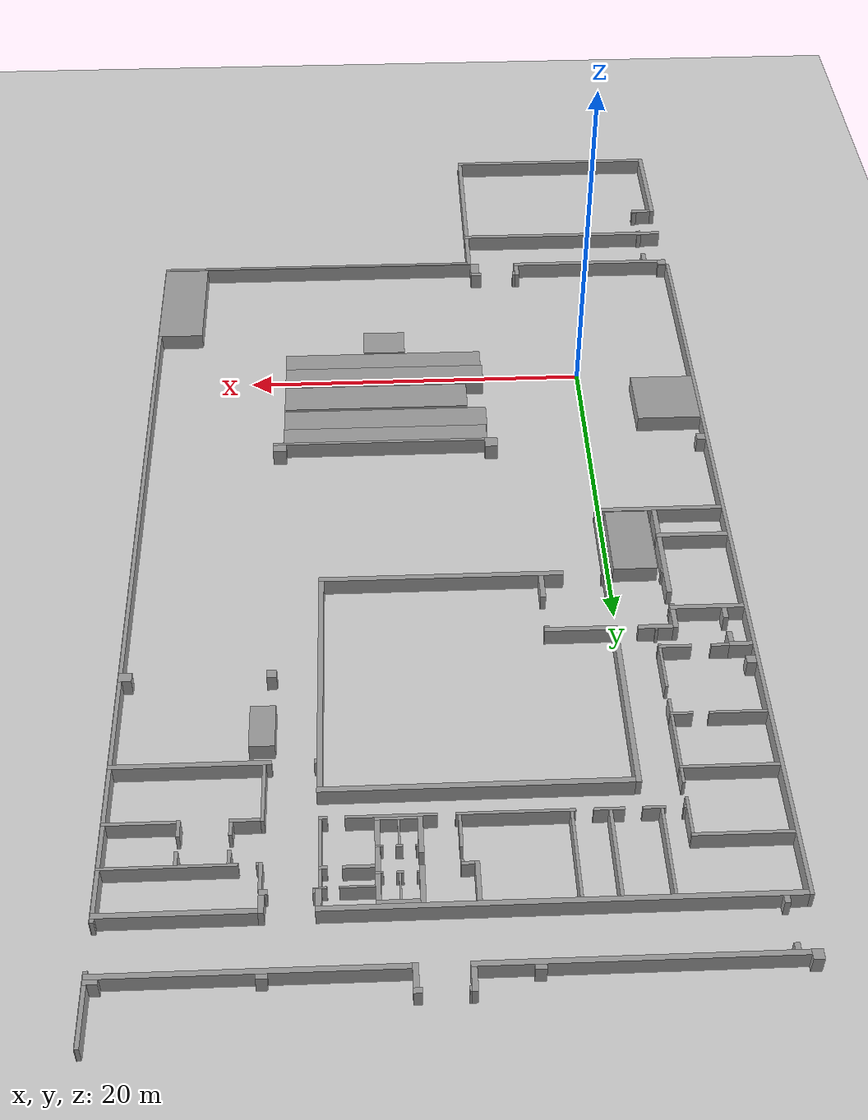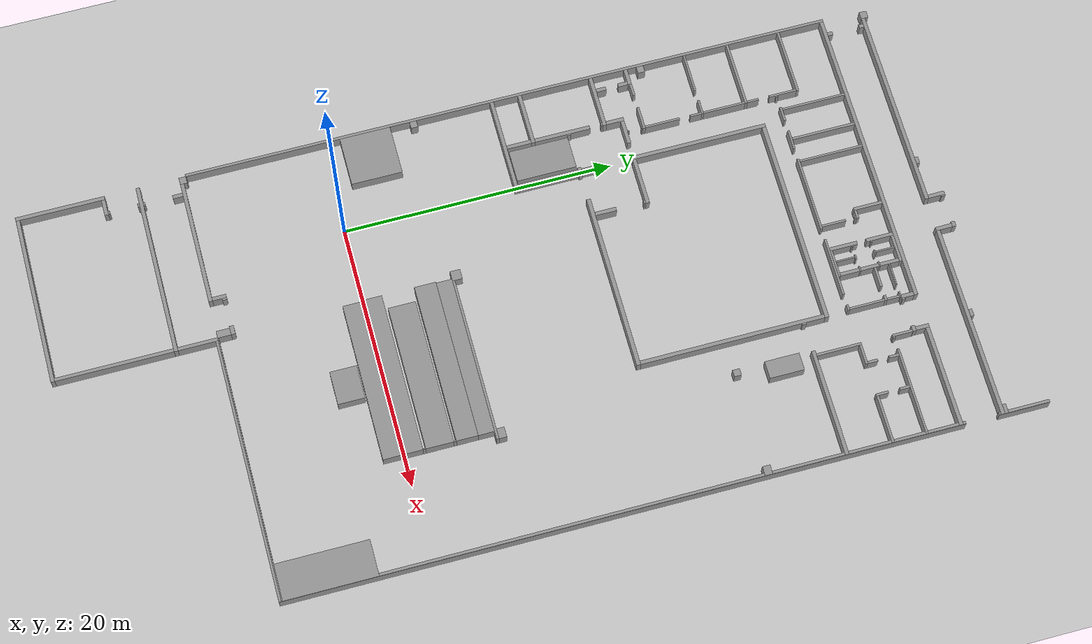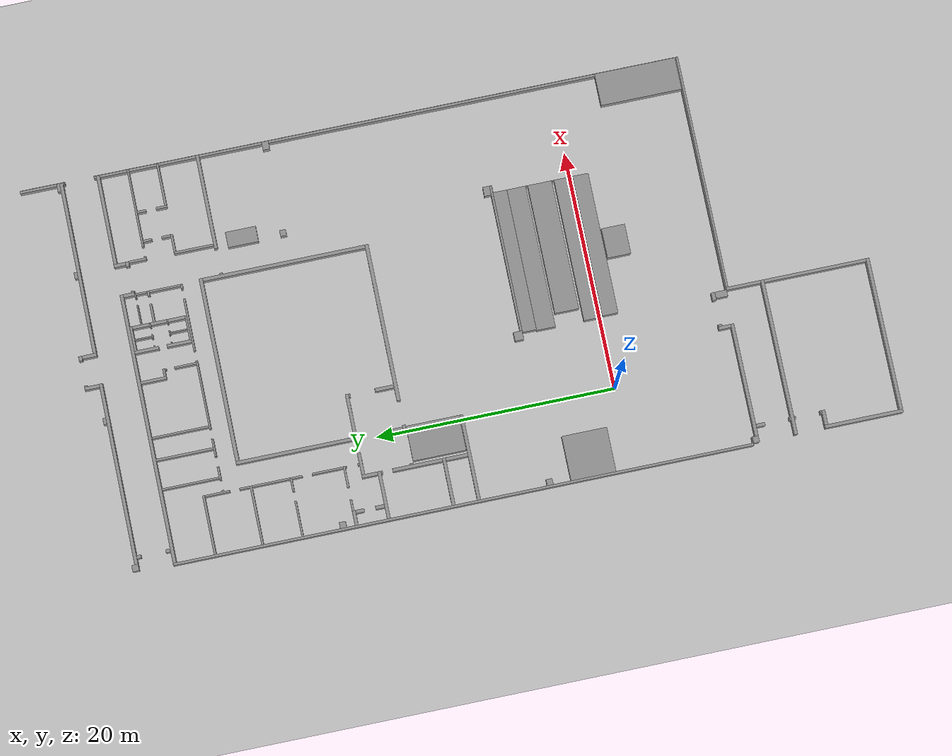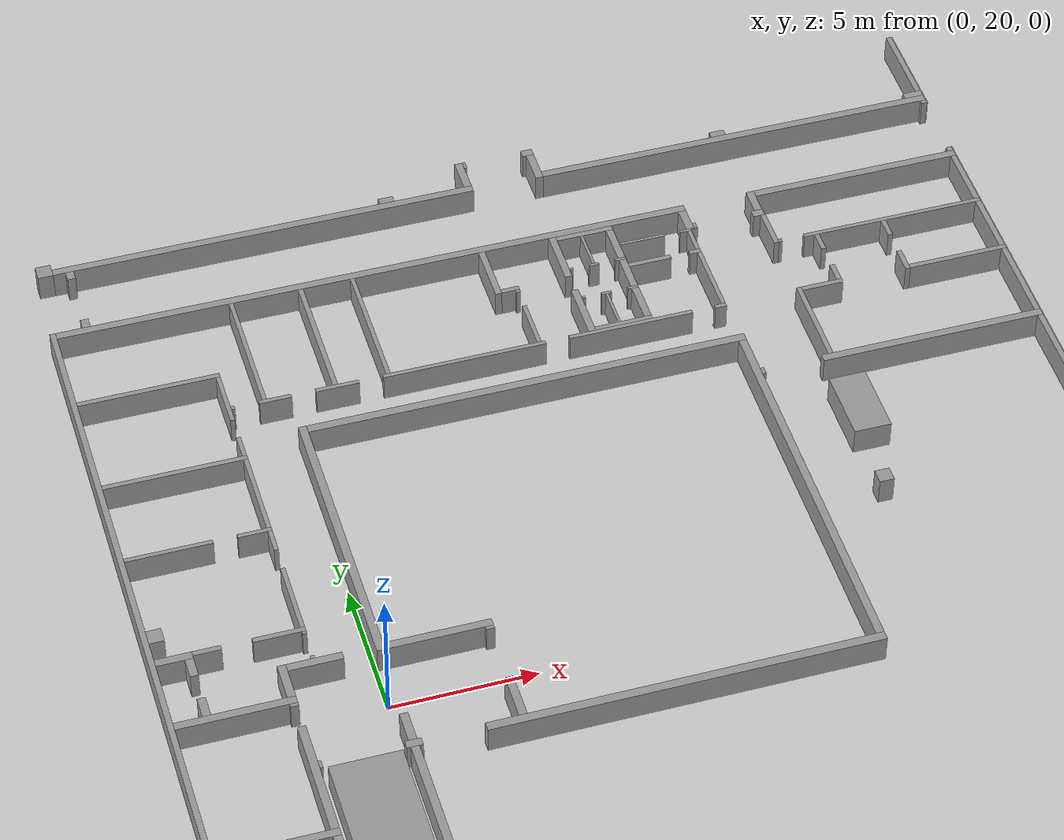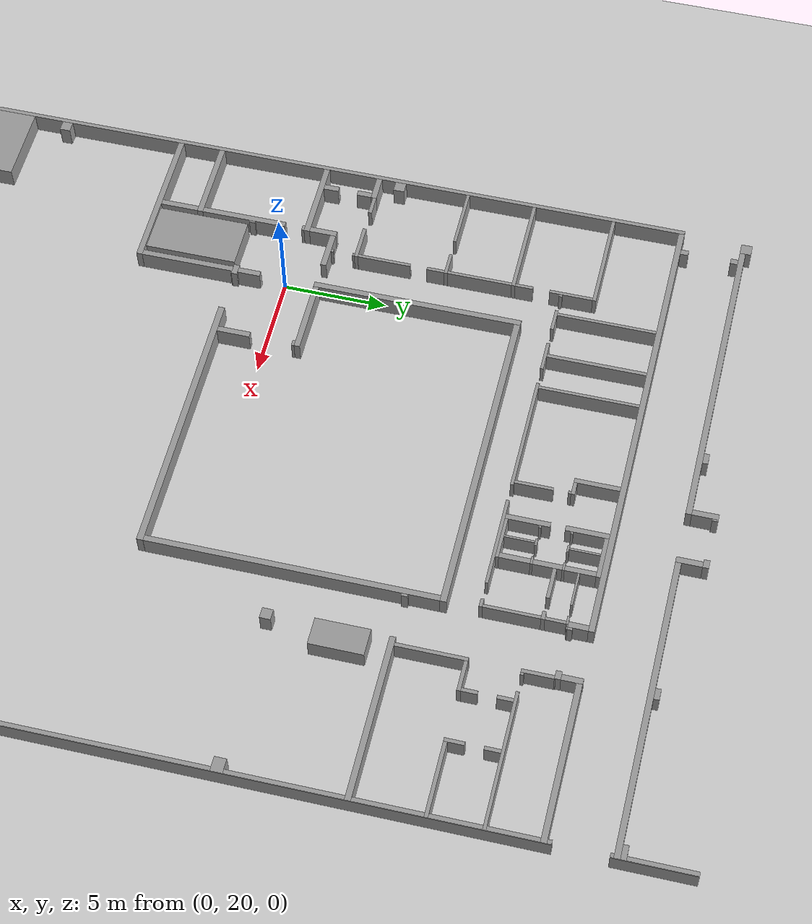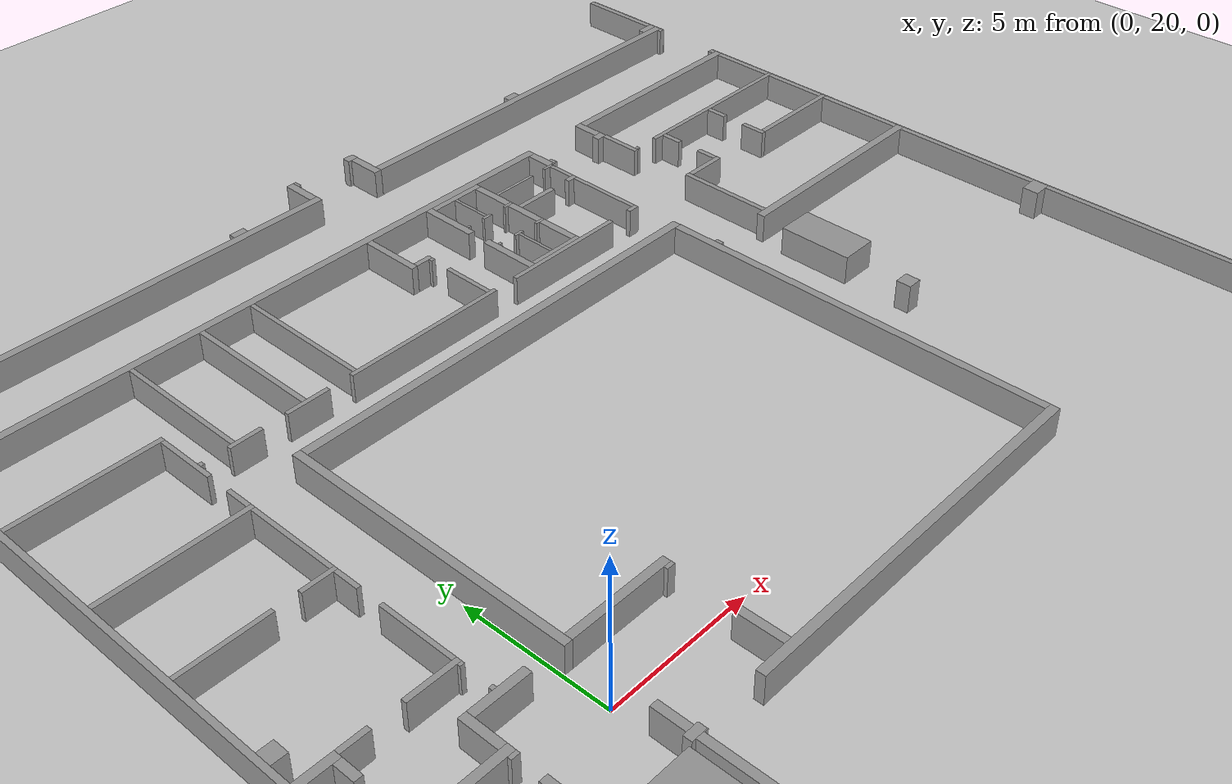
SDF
<sdf version='1.4'>
  <world name='default'>
    <!-- Default physics configuration -->
    <physics type='ode'>
      <gravity>0.000000 0.000000 -9.810000</gravity>
      <ode>
        <solver>
          <type>quick</type>
          <iters>20</iters>
          <sor>1.000000</sor>
        </solver>
        <constraints>
          <cfm>0.000000</cfm>
          <erp>0.200000</erp>
          <contact_max_correcting_vel>100.000000</contact_max_correcting_vel>
          <contact_surface_layer>0.000000</contact_surface_layer>
        </constraints>
      </ode>
      <real_time_update_rate>1000.000000</real_time_update_rate>
      <max_step_size>0.001000</max_step_size>
      <real_time_factor>1.000000</real_time_factor>
      <max_contacts>20</max_contacts>
    </physics>

    <!-- A global light source -->
    <include>
      <uri>model://sun</uri>
    </include>

    <!-- A ground plane -->
    <include>
      <uri>model://ground_plane</uri>
    </include>

    <!-- Walls -->
    <include>
      <uri>model://adler_erfurt_shop_upstairs</uri>
      <name>walls</name>
      <pose>-7 -22.75 0 0 0 1.5708</pose>
    </include>

    <!-- Camera Position -->
    <gui fullscreen='0'>
      <camera name='user_camera'>
        <pose>5.694260 7.254210 18.725000 0.000000 1.145800 -3.134990</pose>
        <view_controller>orbit</view_controller>
      </camera>
    </gui>
  </world>
</sdf>

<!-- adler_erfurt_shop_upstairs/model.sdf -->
<sdf version="1.4">
  <model name="AdlerErfurtShopUpstairs">
    <static>1</static>
    <link name="Wall_0">
      <collision name="Wall_0_Collision">
        <geometry>
          <box>
            <size>48.51064 0.20426 1.00000</size>
          </box>
        </geometry>
        <pose>36.84255 -0.10213 0.50000 0 0 0.00000</pose>
      </collision>
      <visual name="Wall_0_Visual">
        <geometry>
          <box>
            <size>48.51064 0.20426 1.00000</size>
          </box>
        </geometry>
        <material>
          <script>
            <uri>file://media/materials/scripts/gazebo.material</uri>
            <name>Gazebo/Grey</name>
          </script>
        </material>
        <pose>36.84255 -0.10213 0.50000 0 0 0.00000</pose>
      </visual>
    </link>
    <link name="Wall_1">
      <collision name="Wall_1_Collision">
        <geometry>
          <box>
            <size>6.56170 0.28085 1.00000</size>
          </box>
        </geometry>
        <pose>3.28085 -0.31915 0.50000 0 0 0.00000</pose>
      </collision>
      <visual name="Wall_1_Visual">
        <geometry>
          <box>
            <size>6.56170 0.28085 1.00000</size>
          </box>
        </geometry>
        <material>
          <script>
            <uri>file://media/materials/scripts/gazebo.material</uri>
            <name>Gazebo/Grey</name>
          </script>
        </material>
        <pose>3.28085 -0.31915 0.50000 0 0 0.00000</pose>
      </visual>
    </link>
    <link name="Wall_2">
      <collision name="Wall_2_Collision">
        <geometry>
          <box>
            <size>0.28085 13.07234 1.00000</size>
          </box>
        </geometry>
        <pose>9.02553 -6.71489 0.50000 0 0 0.00000</pose>
      </collision>
      <visual name="Wall_2_Visual">
        <geometry>
          <box>
            <size>0.28085 13.07234 1.00000</size>
          </box>
        </geometry>
        <material>
          <script>
            <uri>file://media/materials/scripts/gazebo.material</uri>
            <name>Gazebo/Grey</name>
          </script>
        </material>
        <pose>9.02553 -6.71489 0.50000 0 0 0.00000</pose>
      </visual>
    </link>
    <link name="Wall_3">
      <collision name="Wall_3_Collision">
        <geometry>
          <box>
            <size>0.51064 0.53617 1.00000</size>
          </box>
        </geometry>
        <pose>12.33191 -0.44681 0.50000 0 0 0.00000</pose>
      </collision>
      <visual name="Wall_3_Visual">
        <geometry>
          <box>
            <size>0.51064 0.53617 1.00000</size>
          </box>
        </geometry>
        <material>
          <script>
            <uri>file://media/materials/scripts/gazebo.material</uri>
            <name>Gazebo/Grey</name>
          </script>
        </material>
        <pose>12.33191 -0.44681 0.50000 0 0 0.00000</pose>
      </visual>
    </link>
    <link name="Wall_4">
      <collision name="Wall_4_Collision">
        <geometry>
          <box>
            <size>0.53617 0.53617 1.00000</size>
          </box>
        </geometry>
        <pose>64.17447 -0.44681 0.50000 0 0 0.00000</pose>
      </collision>
      <visual name="Wall_4_Visual">
        <geometry>
          <box>
            <size>0.53617 0.53617 1.00000</size>
          </box>
        </geometry>
        <material>
          <script>
            <uri>file://media/materials/scripts/gazebo.material</uri>
            <name>Gazebo/Grey</name>
          </script>
        </material>
        <pose>64.17447 -0.44681 0.50000 0 0 0.00000</pose>
      </visual>
    </link>
    <link name="Wall_5">
      <collision name="Wall_5_Collision">
        <geometry>
          <box>
            <size>0.05106 0.51064 1.00000</size>
          </box>
        </geometry>
        <pose>12.61277 -0.45957 0.50000 0 0 0.00000</pose>
      </collision>
      <visual name="Wall_5_Visual">
        <geometry>
          <box>
            <size>0.05106 0.51064 1.00000</size>
          </box>
        </geometry>
        <material>
          <script>
            <uri>file://media/materials/scripts/gazebo.material</uri>
            <name>Gazebo/Grey</name>
          </script>
        </material>
        <pose>12.61277 -0.45957 0.50000 0 0 0.00000</pose>
      </visual>
    </link>
    <link name="Wall_6">
      <collision name="Wall_6_Collision">
        <geometry>
          <box>
            <size>3.77872 3.72766 1.00000</size>
          </box>
        </geometry>
        <pose>25.99149 -2.06809 0.50000 0 0 0.00000</pose>
      </collision>
      <visual name="Wall_6_Visual">
        <geometry>
          <box>
            <size>3.77872 3.72766 1.00000</size>
          </box>
        </geometry>
        <material>
          <script>
            <uri>file://media/materials/scripts/gazebo.material</uri>
            <name>Gazebo/Grey</name>
          </script>
        </material>
        <pose>25.99149 -2.06809 0.50000 0 0 0.00000</pose>
      </visual>
    </link>
    <link name="Wall_7">
      <collision name="Wall_7_Collision">
        <geometry>
          <box>
            <size>0.51064 0.51064 1.00000</size>
          </box>
        </geometry>
        <pose>29.61702 -0.45957 0.50000 0 0 0.00000</pose>
      </collision>
      <visual name="Wall_7_Visual">
        <geometry>
          <box>
            <size>0.51064 0.51064 1.00000</size>
          </box>
        </geometry>
        <material>
          <script>
            <uri>file://media/materials/scripts/gazebo.material</uri>
            <name>Gazebo/Grey</name>
          </script>
        </material>
        <pose>29.61702 -0.45957 0.50000 0 0 0.00000</pose>
      </visual>
    </link>
    <link name="Wall_8">
      <collision name="Wall_8_Collision">
        <geometry>
          <box>
            <size>0.28085 7.14894 1.00000</size>
          </box>
        </geometry>
        <pose>35.57872 -3.77872 0.50000 0 0 0.00000</pose>
      </collision>
      <visual name="Wall_8_Visual">
        <geometry>
          <box>
            <size>0.28085 7.14894 1.00000</size>
          </box>
        </geometry>
        <material>
          <script>
            <uri>file://media/materials/scripts/gazebo.material</uri>
            <name>Gazebo/Grey</name>
          </script>
        </material>
        <pose>35.57872 -3.77872 0.50000 0 0 0.00000</pose>
      </visual>
    </link>
    <link name="Wall_9">
      <collision name="Wall_9_Collision">
        <geometry>
          <box>
            <size>0.28085 3.95745 1.00000</size>
          </box>
        </geometry>
        <pose>37.69787 -2.18298 0.50000 0 0 0.00000</pose>
      </collision>
      <visual name="Wall_9_Visual">
        <geometry>
          <box>
            <size>0.28085 3.95745 1.00000</size>
          </box>
        </geometry>
        <material>
          <script>
            <uri>file://media/materials/scripts/gazebo.material</uri>
            <name>Gazebo/Grey</name>
          </script>
        </material>
        <pose>37.69787 -2.18298 0.50000 0 0 0.00000</pose>
      </visual>
    </link>
    <link name="Wall_10">
      <collision name="Wall_10_Collision">
        <geometry>
          <box>
            <size>0.28085 3.95745 1.00000</size>
          </box>
        </geometry>
        <pose>43.11064 -2.18298 0.50000 0 0 0.00000</pose>
      </collision>
      <visual name="Wall_10_Visual">
        <geometry>
          <box>
            <size>0.28085 3.95745 1.00000</size>
          </box>
        </geometry>
        <material>
          <script>
            <uri>file://media/materials/scripts/gazebo.material</uri>
            <name>Gazebo/Grey</name>
          </script>
        </material>
        <pose>43.11064 -2.18298 0.50000 0 0 0.00000</pose>
      </visual>
    </link>
    <link name="Wall_11">
      <collision name="Wall_11_Collision">
        <geometry>
          <box>
            <size>0.28085 1.22553 1.00000</size>
          </box>
        </geometry>
        <pose>45.79149 -0.81702 0.50000 0 0 0.00000</pose>
      </collision>
      <visual name="Wall_11_Visual">
        <geometry>
          <box>
            <size>0.28085 1.22553 1.00000</size>
          </box>
        </geometry>
        <material>
          <script>
            <uri>file://media/materials/scripts/gazebo.material</uri>
            <name>Gazebo/Grey</name>
          </script>
        </material>
        <pose>45.79149 -0.81702 0.50000 0 0 0.00000</pose>
      </visual>
    </link>
    <link name="Wall_12">
      <collision name="Wall_12_Collision">
        <geometry>
          <box>
            <size>0.53617 0.51064 1.00000</size>
          </box>
        </geometry>
        <pose>46.88936 -0.45957 0.50000 0 0 0.00000</pose>
      </collision>
      <visual name="Wall_12_Visual">
        <geometry>
          <box>
            <size>0.53617 0.51064 1.00000</size>
          </box>
        </geometry>
        <material>
          <script>
            <uri>file://media/materials/scripts/gazebo.material</uri>
            <name>Gazebo/Grey</name>
          </script>
        </material>
        <pose>46.88936 -0.45957 0.50000 0 0 0.00000</pose>
      </visual>
    </link>
    <link name="Wall_13">
      <collision name="Wall_13_Collision">
        <geometry>
          <box>
            <size>0.15319 2.96170 1.00000</size>
          </box>
        </geometry>
        <pose>50.29787 -1.68511 0.50000 0 0 0.00000</pose>
      </collision>
      <visual name="Wall_13_Visual">
        <geometry>
          <box>
            <size>0.15319 2.96170 1.00000</size>
          </box>
        </geometry>
        <material>
          <script>
            <uri>file://media/materials/scripts/gazebo.material</uri>
            <name>Gazebo/Grey</name>
          </script>
        </material>
        <pose>50.29787 -1.68511 0.50000 0 0 0.00000</pose>
      </visual>
    </link>
    <link name="Wall_14">
      <collision name="Wall_14_Collision">
        <geometry>
          <box>
            <size>0.17872 4.92766 1.00000</size>
          </box>
        </geometry>
        <pose>53.62979 -2.66809 0.50000 0 0 0.00000</pose>
      </collision>
      <visual name="Wall_14_Visual">
        <geometry>
          <box>
            <size>0.17872 4.92766 1.00000</size>
          </box>
        </geometry>
        <material>
          <script>
            <uri>file://media/materials/scripts/gazebo.material</uri>
            <name>Gazebo/Grey</name>
          </script>
        </material>
        <pose>53.62979 -2.66809 0.50000 0 0 0.00000</pose>
      </visual>
    </link>
    <link name="Wall_15">
      <collision name="Wall_15_Collision">
        <geometry>
          <box>
            <size>0.17872 4.92766 1.00000</size>
          </box>
        </geometry>
        <pose>57.58723 -2.66809 0.50000 0 0 0.00000</pose>
      </collision>
      <visual name="Wall_15_Visual">
        <geometry>
          <box>
            <size>0.17872 4.92766 1.00000</size>
          </box>
        </geometry>
        <material>
          <script>
            <uri>file://media/materials/scripts/gazebo.material</uri>
            <name>Gazebo/Grey</name>
          </script>
        </material>
        <pose>57.58723 -2.66809 0.50000 0 0 0.00000</pose>
      </visual>
    </link>
    <link name="Wall_16">
      <collision name="Wall_16_Collision">
        <geometry>
          <box>
            <size>0.28085 22.57021 1.00000</size>
          </box>
        </geometry>
        <pose>60.95745 -11.48936 0.50000 0 0 0.00000</pose>
      </collision>
      <visual name="Wall_16_Visual">
        <geometry>
          <box>
            <size>0.28085 22.57021 1.00000</size>
          </box>
        </geometry>
        <material>
          <script>
            <uri>file://media/materials/scripts/gazebo.material</uri>
            <name>Gazebo/Grey</name>
          </script>
        </material>
        <pose>60.95745 -11.48936 0.50000 0 0 0.00000</pose>
      </visual>
    </link>
    <link name="Wall_17">
      <collision name="Wall_17_Collision">
        <geometry>
          <box>
            <size>0.28085 12.79149 1.00000</size>
          </box>
        </geometry>
        <pose>0.14043 -6.85532 0.50000 0 0 0.00000</pose>
      </collision>
      <visual name="Wall_17_Visual">
        <geometry>
          <box>
            <size>0.28085 12.79149 1.00000</size>
          </box>
        </geometry>
        <material>
          <script>
            <uri>file://media/materials/scripts/gazebo.material</uri>
            <name>Gazebo/Grey</name>
          </script>
        </material>
        <pose>0.14043 -6.85532 0.50000 0 0 0.00000</pose>
      </visual>
    </link>
    <link name="Wall_18">
      <collision name="Wall_18_Collision">
        <geometry>
          <box>
            <size>0.28085 1.22553 1.00000</size>
          </box>
        </geometry>
        <pose>6.42128 -1.07234 0.50000 0 0 0.00000</pose>
      </collision>
      <visual name="Wall_18_Visual">
        <geometry>
          <box>
            <size>0.28085 1.22553 1.00000</size>
          </box>
        </geometry>
        <material>
          <script>
            <uri>file://media/materials/scripts/gazebo.material</uri>
            <name>Gazebo/Grey</name>
          </script>
        </material>
        <pose>6.42128 -1.07234 0.50000 0 0 0.00000</pose>
      </visual>
    </link>
    <link name="Wall_19">
      <collision name="Wall_19_Collision">
        <geometry>
          <box>
            <size>0.28085 9.47234 1.00000</size>
          </box>
        </geometry>
        <pose>12.21702 -5.45106 0.50000 0 0 0.00000</pose>
      </collision>
      <visual name="Wall_19_Visual">
        <geometry>
          <box>
            <size>0.28085 9.47234 1.00000</size>
          </box>
        </geometry>
        <material>
          <script>
            <uri>file://media/materials/scripts/gazebo.material</uri>
            <name>Gazebo/Grey</name>
          </script>
        </material>
        <pose>12.21702 -5.45106 0.50000 0 0 0.00000</pose>
      </visual>
    </link>
    <link name="Wall_20">
      <collision name="Wall_20_Collision">
        <geometry>
          <box>
            <size>0.28085 15.16596 1.00000</size>
          </box>
        </geometry>
        <pose>64.04681 -8.29787 0.50000 0 0 0.00000</pose>
      </collision>
      <visual name="Wall_20_Visual">
        <geometry>
          <box>
            <size>0.28085 15.16596 1.00000</size>
          </box>
        </geometry>
        <material>
          <script>
            <uri>file://media/materials/scripts/gazebo.material</uri>
            <name>Gazebo/Grey</name>
          </script>
        </material>
        <pose>64.04681 -8.29787 0.50000 0 0 0.00000</pose>
      </visual>
    </link>
    <link name="Wall_21">
      <collision name="Wall_21_Collision">
        <geometry>
          <box>
            <size>0.74043 0.28085 1.00000</size>
          </box>
        </geometry>
        <pose>43.62128 -1.28936 0.50000 0 0 0.00000</pose>
      </collision>
      <visual name="Wall_21_Visual">
        <geometry>
          <box>
            <size>0.74043 0.28085 1.00000</size>
          </box>
        </geometry>
        <material>
          <script>
            <uri>file://media/materials/scripts/gazebo.material</uri>
            <name>Gazebo/Grey</name>
          </script>
        </material>
        <pose>43.62128 -1.28936 0.50000 0 0 0.00000</pose>
      </visual>
    </link>
    <link name="Wall_22">
      <collision name="Wall_22_Collision">
        <geometry>
          <box>
            <size>0.71489 0.28085 1.00000</size>
          </box>
        </geometry>
        <pose>45.29362 -1.28936 0.50000 0 0 0.00000</pose>
      </collision>
      <visual name="Wall_22_Visual">
        <geometry>
          <box>
            <size>0.71489 0.28085 1.00000</size>
          </box>
        </geometry>
        <material>
          <script>
            <uri>file://media/materials/scripts/gazebo.material</uri>
            <name>Gazebo/Grey</name>
          </script>
        </material>
        <pose>45.29362 -1.28936 0.50000 0 0 0.00000</pose>
      </visual>
    </link>
    <link name="Wall_23">
      <collision name="Wall_23_Collision">
        <geometry>
          <box>
            <size>0.38298 0.28085 1.00000</size>
          </box>
        </geometry>
        <pose>61.28936 -1.28936 0.50000 0 0 0.00000</pose>
      </collision>
      <visual name="Wall_23_Visual">
        <geometry>
          <box>
            <size>0.38298 0.28085 1.00000</size>
          </box>
        </geometry>
        <material>
          <script>
            <uri>file://media/materials/scripts/gazebo.material</uri>
            <name>Gazebo/Grey</name>
          </script>
        </material>
        <pose>61.28936 -1.28936 0.50000 0 0 0.00000</pose>
      </visual>
    </link>
    <link name="Wall_24">
      <collision name="Wall_24_Collision">
        <geometry>
          <box>
            <size>0.35745 0.28085 1.00000</size>
          </box>
        </geometry>
        <pose>63.72766 -1.28936 0.50000 0 0 0.00000</pose>
      </collision>
      <visual name="Wall_24_Visual">
        <geometry>
          <box>
            <size>0.35745 0.28085 1.00000</size>
          </box>
        </geometry>
        <material>
          <script>
            <uri>file://media/materials/scripts/gazebo.material</uri>
            <name>Gazebo/Grey</name>
          </script>
        </material>
        <pose>63.72766 -1.28936 0.50000 0 0 0.00000</pose>
      </visual>
    </link>
    <link name="Wall_25">
      <collision name="Wall_25_Collision">
        <geometry>
          <box>
            <size>0.12766 0.28085 1.00000</size>
          </box>
        </geometry>
        <pose>6.62553 -1.54468 0.50000 0 0 0.00000</pose>
      </collision>
      <visual name="Wall_25_Visual">
        <geometry>
          <box>
            <size>0.12766 0.28085 1.00000</size>
          </box>
        </geometry>
        <material>
          <script>
            <uri>file://media/materials/scripts/gazebo.material</uri>
            <name>Gazebo/Grey</name>
          </script>
        </material>
        <pose>6.62553 -1.54468 0.50000 0 0 0.00000</pose>
      </visual>
    </link>
    <link name="Wall_26">
      <collision name="Wall_26_Collision">
        <geometry>
          <box>
            <size>0.12766 0.28085 1.00000</size>
          </box>
        </geometry>
        <pose>8.82128 -1.54468 0.50000 0 0 0.00000</pose>
      </collision>
      <visual name="Wall_26_Visual">
        <geometry>
          <box>
            <size>0.12766 0.28085 1.00000</size>
          </box>
        </geometry>
        <material>
          <script>
            <uri>file://media/materials/scripts/gazebo.material</uri>
            <name>Gazebo/Grey</name>
          </script>
        </material>
        <pose>8.82128 -1.54468 0.50000 0 0 0.00000</pose>
      </visual>
    </link>
    <link name="Wall_27">
      <collision name="Wall_27_Collision">
        <geometry>
          <box>
            <size>0.12766 0.28085 1.00000</size>
          </box>
        </geometry>
        <pose>9.22979 -1.54468 0.50000 0 0 0.00000</pose>
      </collision>
      <visual name="Wall_27_Visual">
        <geometry>
          <box>
            <size>0.12766 0.28085 1.00000</size>
          </box>
        </geometry>
        <material>
          <script>
            <uri>file://media/materials/scripts/gazebo.material</uri>
            <name>Gazebo/Grey</name>
          </script>
        </material>
        <pose>9.22979 -1.54468 0.50000 0 0 0.00000</pose>
      </visual>
    </link>
    <link name="Wall_28">
      <collision name="Wall_28_Collision">
        <geometry>
          <box>
            <size>0.74043 0.28085 1.00000</size>
          </box>
        </geometry>
        <pose>11.70638 -1.54468 0.50000 0 0 0.00000</pose>
      </collision>
      <visual name="Wall_28_Visual">
        <geometry>
          <box>
            <size>0.74043 0.28085 1.00000</size>
          </box>
        </geometry>
        <material>
          <script>
            <uri>file://media/materials/scripts/gazebo.material</uri>
            <name>Gazebo/Grey</name>
          </script>
        </material>
        <pose>11.70638 -1.54468 0.50000 0 0 0.00000</pose>
      </visual>
    </link>
    <link name="Wall_29">
      <collision name="Wall_29_Collision">
        <geometry>
          <box>
            <size>0.17872 0.94468 1.00000</size>
          </box>
        </geometry>
        <pose>45.84255 -1.90213 0.50000 0 0 0.00000</pose>
      </collision>
      <visual name="Wall_29_Visual">
        <geometry>
          <box>
            <size>0.17872 0.94468 1.00000</size>
          </box>
        </geometry>
        <material>
          <script>
            <uri>file://media/materials/scripts/gazebo.material</uri>
            <name>Gazebo/Grey</name>
          </script>
        </material>
        <pose>45.84255 -1.90213 0.50000 0 0 0.00000</pose>
      </visual>
    </link>
    <link name="Wall_30">
      <collision name="Wall_30_Collision">
        <geometry>
          <box>
            <size>0.17872 1.73617 1.00000</size>
          </box>
        </geometry>
        <pose>45.84255 -4.26383 0.50000 0 0 0.00000</pose>
      </collision>
      <visual name="Wall_30_Visual">
        <geometry>
          <box>
            <size>0.17872 1.73617 1.00000</size>
          </box>
        </geometry>
        <material>
          <script>
            <uri>file://media/materials/scripts/gazebo.material</uri>
            <name>Gazebo/Grey</name>
          </script>
        </material>
        <pose>45.84255 -4.26383 0.50000 0 0 0.00000</pose>
      </visual>
    </link>
    <link name="Wall_31">
      <collision name="Wall_31_Collision">
        <geometry>
          <box>
            <size>1.83830 0.28085 1.00000</size>
          </box>
        </geometry>
        <pose>36.63830 -4.02128 0.50000 0 0 0.00000</pose>
      </collision>
      <visual name="Wall_31_Visual">
        <geometry>
          <box>
            <size>1.83830 0.28085 1.00000</size>
          </box>
        </geometry>
        <material>
          <script>
            <uri>file://media/materials/scripts/gazebo.material</uri>
            <name>Gazebo/Grey</name>
          </script>
        </material>
        <pose>36.63830 -4.02128 0.50000 0 0 0.00000</pose>
      </visual>
    </link>
    <link name="Wall_32">
      <collision name="Wall_32_Collision">
        <geometry>
          <box>
            <size>4.16170 0.28085 1.00000</size>
          </box>
        </geometry>
        <pose>39.91915 -4.02128 0.50000 0 0 0.00000</pose>
      </collision>
      <visual name="Wall_32_Visual">
        <geometry>
          <box>
            <size>4.16170 0.28085 1.00000</size>
          </box>
        </geometry>
        <material>
          <script>
            <uri>file://media/materials/scripts/gazebo.material</uri>
            <name>Gazebo/Grey</name>
          </script>
        </material>
        <pose>39.91915 -4.02128 0.50000 0 0 0.00000</pose>
      </visual>
    </link>
    <link name="Wall_33">
      <collision name="Wall_33_Collision">
        <geometry>
          <box>
            <size>0.12766 0.28085 1.00000</size>
          </box>
        </geometry>
        <pose>42.90638 -4.02128 0.50000 0 0 0.00000</pose>
      </collision>
      <visual name="Wall_33_Visual">
        <geometry>
          <box>
            <size>0.12766 0.28085 1.00000</size>
          </box>
        </geometry>
        <material>
          <script>
            <uri>file://media/materials/scripts/gazebo.material</uri>
            <name>Gazebo/Grey</name>
          </script>
        </material>
        <pose>42.90638 -4.02128 0.50000 0 0 0.00000</pose>
      </visual>
    </link>
    <link name="Wall_34">
      <collision name="Wall_34_Collision">
        <geometry>
          <box>
            <size>1.32766 0.28085 1.00000</size>
          </box>
        </geometry>
        <pose>43.91489 -4.02128 0.50000 0 0 0.00000</pose>
      </collision>
      <visual name="Wall_34_Visual">
        <geometry>
          <box>
            <size>1.32766 0.28085 1.00000</size>
          </box>
        </geometry>
        <material>
          <script>
            <uri>file://media/materials/scripts/gazebo.material</uri>
            <name>Gazebo/Grey</name>
          </script>
        </material>
        <pose>43.91489 -4.02128 0.50000 0 0 0.00000</pose>
      </visual>
    </link>
    <link name="Wall_35">
      <collision name="Wall_35_Collision">
        <geometry>
          <box>
            <size>0.15319 1.14894 1.00000</size>
          </box>
        </geometry>
        <pose>50.29787 -4.55745 0.50000 0 0 0.00000</pose>
      </collision>
      <visual name="Wall_35_Visual">
        <geometry>
          <box>
            <size>0.15319 1.14894 1.00000</size>
          </box>
        </geometry>
        <material>
          <script>
            <uri>file://media/materials/scripts/gazebo.material</uri>
            <name>Gazebo/Grey</name>
          </script>
        </material>
        <pose>50.29787 -4.55745 0.50000 0 0 0.00000</pose>
      </visual>
    </link>
    <link name="Wall_36">
      <collision name="Wall_36_Collision">
        <geometry>
          <box>
            <size>0.28085 0.10213 1.00000</size>
          </box>
        </geometry>
        <pose>40.37872 -4.21277 0.50000 0 0 0.00000</pose>
      </collision>
      <visual name="Wall_36_Visual">
        <geometry>
          <box>
            <size>0.28085 0.10213 1.00000</size>
          </box>
        </geometry>
        <material>
          <script>
            <uri>file://media/materials/scripts/gazebo.material</uri>
            <name>Gazebo/Grey</name>
          </script>
        </material>
        <pose>40.37872 -4.21277 0.50000 0 0 0.00000</pose>
      </visual>
    </link>
    <link name="Wall_37">
      <collision name="Wall_37_Collision">
        <geometry>
          <box>
            <size>0.28085 1.83830 1.00000</size>
          </box>
        </geometry>
        <pose>44.43830 -5.08085 0.50000 0 0 0.00000</pose>
      </collision>
      <visual name="Wall_37_Visual">
        <geometry>
          <box>
            <size>0.28085 1.83830 1.00000</size>
          </box>
        </geometry>
        <material>
          <script>
            <uri>file://media/materials/scripts/gazebo.material</uri>
            <name>Gazebo/Grey</name>
          </script>
        </material>
        <pose>44.43830 -5.08085 0.50000 0 0 0.00000</pose>
      </visual>
    </link>
    <link name="Wall_38">
      <collision name="Wall_38_Collision">
        <geometry>
          <box>
            <size>4.44255 2.40000 1.00000</size>
          </box>
        </geometry>
        <pose>37.99149 -5.61702 0.50000 0 0 0.00000</pose>
      </collision>
      <visual name="Wall_38_Visual">
        <geometry>
          <box>
            <size>4.44255 2.40000 1.00000</size>
          </box>
        </geometry>
        <material>
          <script>
            <uri>file://media/materials/scripts/gazebo.material</uri>
            <name>Gazebo/Grey</name>
          </script>
        </material>
        <pose>37.99149 -5.61702 0.50000 0 0 0.00000</pose>
      </visual>
    </link>
    <link name="Wall_39">
      <collision name="Wall_39_Collision">
        <geometry>
          <box>
            <size>0.12766 0.15319 1.00000</size>
          </box>
        </geometry>
        <pose>44.64255 -5.05532 0.50000 0 0 0.00000</pose>
      </collision>
      <visual name="Wall_39_Visual">
        <geometry>
          <box>
            <size>0.12766 0.15319 1.00000</size>
          </box>
        </geometry>
        <material>
          <script>
            <uri>file://media/materials/scripts/gazebo.material</uri>
            <name>Gazebo/Grey</name>
          </script>
        </material>
        <pose>44.64255 -5.05532 0.50000 0 0 0.00000</pose>
      </visual>
    </link>
    <link name="Wall_40">
      <collision name="Wall_40_Collision">
        <geometry>
          <box>
            <size>0.10213 0.15319 1.00000</size>
          </box>
        </geometry>
        <pose>45.70213 -5.05532 0.50000 0 0 0.00000</pose>
      </collision>
      <visual name="Wall_40_Visual">
        <geometry>
          <box>
            <size>0.10213 0.15319 1.00000</size>
          </box>
        </geometry>
        <material>
          <script>
            <uri>file://media/materials/scripts/gazebo.material</uri>
            <name>Gazebo/Grey</name>
          </script>
        </material>
        <pose>45.70213 -5.05532 0.50000 0 0 0.00000</pose>
      </visual>
    </link>
    <link name="Wall_41">
      <collision name="Wall_41_Collision">
        <geometry>
          <box>
            <size>2.60426 0.15319 1.00000</size>
          </box>
        </geometry>
        <pose>47.23404 -5.05532 0.50000 0 0 0.00000</pose>
      </collision>
      <visual name="Wall_41_Visual">
        <geometry>
          <box>
            <size>2.60426 0.15319 1.00000</size>
          </box>
        </geometry>
        <material>
          <script>
            <uri>file://media/materials/scripts/gazebo.material</uri>
            <name>Gazebo/Grey</name>
          </script>
        </material>
        <pose>47.23404 -5.05532 0.50000 0 0 0.00000</pose>
      </visual>
    </link>
    <link name="Wall_42">
      <collision name="Wall_42_Collision">
        <geometry>
          <box>
            <size>0.86809 0.15319 1.00000</size>
          </box>
        </geometry>
        <pose>49.78723 -5.05532 0.50000 0 0 0.00000</pose>
      </collision>
      <visual name="Wall_42_Visual">
        <geometry>
          <box>
            <size>0.86809 0.15319 1.00000</size>
          </box>
        </geometry>
        <material>
          <script>
            <uri>file://media/materials/scripts/gazebo.material</uri>
            <name>Gazebo/Grey</name>
          </script>
        </material>
        <pose>49.78723 -5.05532 0.50000 0 0 0.00000</pose>
      </visual>
    </link>
    <link name="Wall_43">
      <collision name="Wall_43_Collision">
        <geometry>
          <box>
            <size>3.16596 0.15319 1.00000</size>
          </box>
        </geometry>
        <pose>51.95745 -5.05532 0.50000 0 0 0.00000</pose>
      </collision>
      <visual name="Wall_43_Visual">
        <geometry>
          <box>
            <size>3.16596 0.15319 1.00000</size>
          </box>
        </geometry>
        <material>
          <script>
            <uri>file://media/materials/scripts/gazebo.material</uri>
            <name>Gazebo/Grey</name>
          </script>
        </material>
        <pose>51.95745 -5.05532 0.50000 0 0 0.00000</pose>
      </visual>
    </link>
    <link name="Wall_44">
      <collision name="Wall_44_Collision">
        <geometry>
          <box>
            <size>0.86809 0.15319 1.00000</size>
          </box>
        </geometry>
        <pose>54.15319 -5.05532 0.50000 0 0 0.00000</pose>
      </collision>
      <visual name="Wall_44_Visual">
        <geometry>
          <box>
            <size>0.86809 0.15319 1.00000</size>
          </box>
        </geometry>
        <material>
          <script>
            <uri>file://media/materials/scripts/gazebo.material</uri>
            <name>Gazebo/Grey</name>
          </script>
        </material>
        <pose>54.15319 -5.05532 0.50000 0 0 0.00000</pose>
      </visual>
    </link>
    <link name="Wall_45">
      <collision name="Wall_45_Collision">
        <geometry>
          <box>
            <size>2.09362 0.15319 1.00000</size>
          </box>
        </geometry>
        <pose>56.45106 -5.05532 0.50000 0 0 0.00000</pose>
      </collision>
      <visual name="Wall_45_Visual">
        <geometry>
          <box>
            <size>2.09362 0.15319 1.00000</size>
          </box>
        </geometry>
        <material>
          <script>
            <uri>file://media/materials/scripts/gazebo.material</uri>
            <name>Gazebo/Grey</name>
          </script>
        </material>
        <pose>56.45106 -5.05532 0.50000 0 0 0.00000</pose>
      </visual>
    </link>
    <link name="Wall_46">
      <collision name="Wall_46_Collision">
        <geometry>
          <box>
            <size>0.15319 0.12766 1.00000</size>
          </box>
        </geometry>
        <pose>55.96596 -5.19574 0.50000 0 0 0.00000</pose>
      </collision>
      <visual name="Wall_46_Visual">
        <geometry>
          <box>
            <size>0.15319 0.12766 1.00000</size>
          </box>
        </geometry>
        <material>
          <script>
            <uri>file://media/materials/scripts/gazebo.material</uri>
            <name>Gazebo/Grey</name>
          </script>
        </material>
        <pose>55.96596 -5.19574 0.50000 0 0 0.00000</pose>
      </visual>
    </link>
    <link name="Wall_47">
      <collision name="Wall_47_Collision">
        <geometry>
          <box>
            <size>0.15319 1.12340 1.00000</size>
          </box>
        </geometry>
        <pose>55.96596 -6.66383 0.50000 0 0 0.00000</pose>
      </collision>
      <visual name="Wall_47_Visual">
        <geometry>
          <box>
            <size>0.15319 1.12340 1.00000</size>
          </box>
        </geometry>
        <material>
          <script>
            <uri>file://media/materials/scripts/gazebo.material</uri>
            <name>Gazebo/Grey</name>
          </script>
        </material>
        <pose>55.96596 -6.66383 0.50000 0 0 0.00000</pose>
      </visual>
    </link>
    <link name="Wall_48">
      <collision name="Wall_48_Collision">
        <geometry>
          <box>
            <size>4.77447 0.15319 1.00000</size>
          </box>
        </geometry>
        <pose>58.42979 -6.30638 0.50000 0 0 0.00000</pose>
      </collision>
      <visual name="Wall_48_Visual">
        <geometry>
          <box>
            <size>4.77447 0.15319 1.00000</size>
          </box>
        </geometry>
        <material>
          <script>
            <uri>file://media/materials/scripts/gazebo.material</uri>
            <name>Gazebo/Grey</name>
          </script>
        </material>
        <pose>58.42979 -6.30638 0.50000 0 0 0.00000</pose>
      </visual>
    </link>
    <link name="Wall_49">
      <collision name="Wall_49_Collision">
        <geometry>
          <box>
            <size>0.28085 0.53617 1.00000</size>
          </box>
        </geometry>
        <pose>40.37872 -7.21277 0.50000 0 0 0.00000</pose>
      </collision>
      <visual name="Wall_49_Visual">
        <geometry>
          <box>
            <size>0.28085 0.53617 1.00000</size>
          </box>
        </geometry>
        <material>
          <script>
            <uri>file://media/materials/scripts/gazebo.material</uri>
            <name>Gazebo/Grey</name>
          </script>
        </material>
        <pose>40.37872 -7.21277 0.50000 0 0 0.00000</pose>
      </visual>
    </link>
    <link name="Wall_50">
      <collision name="Wall_50_Collision">
        <geometry>
          <box>
            <size>4.51915 0.28085 1.00000</size>
          </box>
        </geometry>
        <pose>37.97872 -7.21277 0.50000 0 0 0.00000</pose>
      </collision>
      <visual name="Wall_50_Visual">
        <geometry>
          <box>
            <size>4.51915 0.28085 1.00000</size>
          </box>
        </geometry>
        <material>
          <script>
            <uri>file://media/materials/scripts/gazebo.material</uri>
            <name>Gazebo/Grey</name>
          </script>
        </material>
        <pose>37.97872 -7.21277 0.50000 0 0 0.00000</pose>
      </visual>
    </link>
    <link name="Wall_51">
      <collision name="Wall_51_Collision">
        <geometry>
          <box>
            <size>1.09787 0.28085 1.00000</size>
          </box>
        </geometry>
        <pose>41.06809 -7.21277 0.50000 0 0 0.00000</pose>
      </collision>
      <visual name="Wall_51_Visual">
        <geometry>
          <box>
            <size>1.09787 0.28085 1.00000</size>
          </box>
        </geometry>
        <material>
          <script>
            <uri>file://media/materials/scripts/gazebo.material</uri>
            <name>Gazebo/Grey</name>
          </script>
        </material>
        <pose>41.06809 -7.21277 0.50000 0 0 0.00000</pose>
      </visual>
    </link>
    <link name="Wall_52">
      <collision name="Wall_52_Collision">
        <geometry>
          <box>
            <size>10.16170 0.28085 1.00000</size>
          </box>
        </geometry>
        <pose>49.37872 -7.21277 0.50000 0 0 0.00000</pose>
      </collision>
      <visual name="Wall_52_Visual">
        <geometry>
          <box>
            <size>10.16170 0.28085 1.00000</size>
          </box>
        </geometry>
        <material>
          <script>
            <uri>file://media/materials/scripts/gazebo.material</uri>
            <name>Gazebo/Grey</name>
          </script>
        </material>
        <pose>49.37872 -7.21277 0.50000 0 0 0.00000</pose>
      </visual>
    </link>
    <link name="Wall_53">
      <collision name="Wall_53_Collision">
        <geometry>
          <box>
            <size>0.02553 0.12766 1.00000</size>
          </box>
        </geometry>
        <pose>40.22553 -7.41702 0.50000 0 0 0.00000</pose>
      </collision>
      <visual name="Wall_53_Visual">
        <geometry>
          <box>
            <size>0.02553 0.12766 1.00000</size>
          </box>
        </geometry>
        <material>
          <script>
            <uri>file://media/materials/scripts/gazebo.material</uri>
            <name>Gazebo/Grey</name>
          </script>
        </material>
        <pose>40.22553 -7.41702 0.50000 0 0 0.00000</pose>
      </visual>
    </link>
    <link name="Wall_54">
      <collision name="Wall_54_Collision">
        <geometry>
          <box>
            <size>0.28085 3.57447 1.00000</size>
          </box>
        </geometry>
        <pose>44.43830 -9.14043 0.50000 0 0 0.00000</pose>
      </collision>
      <visual name="Wall_54_Visual">
        <geometry>
          <box>
            <size>0.28085 3.57447 1.00000</size>
          </box>
        </geometry>
        <material>
          <script>
            <uri>file://media/materials/scripts/gazebo.material</uri>
            <name>Gazebo/Grey</name>
          </script>
        </material>
        <pose>44.43830 -9.14043 0.50000 0 0 0.00000</pose>
      </visual>
    </link>
    <link name="Wall_55">
      <collision name="Wall_55_Collision">
        <geometry>
          <box>
            <size>0.30638 15.42128 1.00000</size>
          </box>
        </geometry>
        <pose>54.30638 -15.06383 0.50000 0 0 0.00000</pose>
      </collision>
      <visual name="Wall_55_Visual">
        <geometry>
          <box>
            <size>0.30638 15.42128 1.00000</size>
          </box>
        </geometry>
        <material>
          <script>
            <uri>file://media/materials/scripts/gazebo.material</uri>
            <name>Gazebo/Grey</name>
          </script>
        </material>
        <pose>54.30638 -15.06383 0.50000 0 0 0.00000</pose>
      </visual>
    </link>
    <link name="Wall_56">
      <collision name="Wall_56_Collision">
        <geometry>
          <box>
            <size>0.15319 1.50638 1.00000</size>
          </box>
        </geometry>
        <pose>55.96596 -8.82128 0.50000 0 0 0.00000</pose>
      </collision>
      <visual name="Wall_56_Visual">
        <geometry>
          <box>
            <size>0.15319 1.50638 1.00000</size>
          </box>
        </geometry>
        <material>
          <script>
            <uri>file://media/materials/scripts/gazebo.material</uri>
            <name>Gazebo/Grey</name>
          </script>
        </material>
        <pose>55.96596 -8.82128 0.50000 0 0 0.00000</pose>
      </visual>
    </link>
    <link name="Wall_57">
      <collision name="Wall_57_Collision">
        <geometry>
          <box>
            <size>4.77447 0.17872 1.00000</size>
          </box>
        </geometry>
        <pose>58.42979 -8.77021 0.50000 0 0 0.00000</pose>
      </collision>
      <visual name="Wall_57_Visual">
        <geometry>
          <box>
            <size>4.77447 0.17872 1.00000</size>
          </box>
        </geometry>
        <material>
          <script>
            <uri>file://media/materials/scripts/gazebo.material</uri>
            <name>Gazebo/Grey</name>
          </script>
        </material>
        <pose>58.42979 -8.77021 0.50000 0 0 0.00000</pose>
      </visual>
    </link>
    <link name="Wall_58">
      <collision name="Wall_58_Collision">
        <geometry>
          <box>
            <size>0.30638 13.22553 1.00000</size>
          </box>
        </geometry>
        <pose>40.36596 -16.16170 0.50000 0 0 0.00000</pose>
      </collision>
      <visual name="Wall_58_Visual">
        <geometry>
          <box>
            <size>0.30638 13.22553 1.00000</size>
          </box>
        </geometry>
        <material>
          <script>
            <uri>file://media/materials/scripts/gazebo.material</uri>
            <name>Gazebo/Grey</name>
          </script>
        </material>
        <pose>40.36596 -16.16170 0.50000 0 0 0.00000</pose>
      </visual>
    </link>
    <link name="Wall_59">
      <collision name="Wall_59_Collision">
        <geometry>
          <box>
            <size>1.02128 0.28085 1.00000</size>
          </box>
        </geometry>
        <pose>12.86809 -10.04681 0.50000 0 0 0.00000</pose>
      </collision>
      <visual name="Wall_59_Visual">
        <geometry>
          <box>
            <size>1.02128 0.28085 1.00000</size>
          </box>
        </geometry>
        <material>
          <script>
            <uri>file://media/materials/scripts/gazebo.material</uri>
            <name>Gazebo/Grey</name>
          </script>
        </material>
        <pose>12.86809 -10.04681 0.50000 0 0 0.00000</pose>
      </visual>
    </link>
    <link name="Wall_60">
      <collision name="Wall_60_Collision">
        <geometry>
          <box>
            <size>0.33191 0.15319 1.00000</size>
          </box>
        </geometry>
        <pose>13.21277 -10.26383 0.50000 0 0 0.00000</pose>
      </collision>
      <visual name="Wall_60_Visual">
        <geometry>
          <box>
            <size>0.33191 0.15319 1.00000</size>
          </box>
        </geometry>
        <material>
          <script>
            <uri>file://media/materials/scripts/gazebo.material</uri>
            <name>Gazebo/Grey</name>
          </script>
        </material>
        <pose>13.21277 -10.26383 0.50000 0 0 0.00000</pose>
      </visual>
    </link>
    <link name="Wall_61">
      <collision name="Wall_61_Collision">
        <geometry>
          <box>
            <size>0.15319 5.74468 1.00000</size>
          </box>
        </geometry>
        <pose>55.96596 -13.28936 0.50000 0 0 0.00000</pose>
      </collision>
      <visual name="Wall_61_Visual">
        <geometry>
          <box>
            <size>0.15319 5.74468 1.00000</size>
          </box>
        </geometry>
        <material>
          <script>
            <uri>file://media/materials/scripts/gazebo.material</uri>
            <name>Gazebo/Grey</name>
          </script>
        </material>
        <pose>55.96596 -13.28936 0.50000 0 0 0.00000</pose>
      </visual>
    </link>
    <link name="Wall_62">
      <collision name="Wall_62_Collision">
        <geometry>
          <box>
            <size>4.77447 0.15319 1.00000</size>
          </box>
        </geometry>
        <pose>58.42979 -10.62128 0.50000 0 0 0.00000</pose>
      </collision>
      <visual name="Wall_62_Visual">
        <geometry>
          <box>
            <size>4.77447 0.15319 1.00000</size>
          </box>
        </geometry>
        <material>
          <script>
            <uri>file://media/materials/scripts/gazebo.material</uri>
            <name>Gazebo/Grey</name>
          </script>
        </material>
        <pose>58.42979 -10.62128 0.50000 0 0 0.00000</pose>
      </visual>
    </link>
    <link name="Wall_63">
      <collision name="Wall_63_Collision">
        <geometry>
          <box>
            <size>1.58298 0.28085 1.00000</size>
          </box>
        </geometry>
        <pose>41.31064 -10.78723 0.50000 0 0 0.00000</pose>
      </collision>
      <visual name="Wall_63_Visual">
        <geometry>
          <box>
            <size>1.58298 0.28085 1.00000</size>
          </box>
        </geometry>
        <material>
          <script>
            <uri>file://media/materials/scripts/gazebo.material</uri>
            <name>Gazebo/Grey</name>
          </script>
        </material>
        <pose>41.31064 -10.78723 0.50000 0 0 0.00000</pose>
      </visual>
    </link>
    <link name="Wall_64">
      <collision name="Wall_64_Collision">
        <geometry>
          <box>
            <size>0.12766 0.28085 1.00000</size>
          </box>
        </geometry>
        <pose>44.23404 -10.78723 0.50000 0 0 0.00000</pose>
      </collision>
      <visual name="Wall_64_Visual">
        <geometry>
          <box>
            <size>0.12766 0.28085 1.00000</size>
          </box>
        </geometry>
        <material>
          <script>
            <uri>file://media/materials/scripts/gazebo.material</uri>
            <name>Gazebo/Grey</name>
          </script>
        </material>
        <pose>44.23404 -10.78723 0.50000 0 0 0.00000</pose>
      </visual>
    </link>
    <link name="Wall_65">
      <collision name="Wall_65_Collision">
        <geometry>
          <box>
            <size>0.30638 0.66383 1.00000</size>
          </box>
        </geometry>
        <pose>13.22553 -12.71489 0.50000 0 0 0.00000</pose>
      </collision>
      <visual name="Wall_65_Visual">
        <geometry>
          <box>
            <size>0.30638 0.66383 1.00000</size>
          </box>
        </geometry>
        <material>
          <script>
            <uri>file://media/materials/scripts/gazebo.material</uri>
            <name>Gazebo/Grey</name>
          </script>
        </material>
        <pose>13.22553 -12.71489 0.50000 0 0 0.00000</pose>
      </visual>
    </link>
    <link name="Wall_66">
      <collision name="Wall_66_Collision">
        <geometry>
          <box>
            <size>0.74043 0.74043 1.00000</size>
          </box>
        </geometry>
        <pose>29.62979 -12.77872 0.50000 0 0 0.00000</pose>
      </collision>
      <visual name="Wall_66_Visual">
        <geometry>
          <box>
            <size>0.74043 0.74043 1.00000</size>
          </box>
        </geometry>
        <material>
          <script>
            <uri>file://media/materials/scripts/gazebo.material</uri>
            <name>Gazebo/Grey</name>
          </script>
        </material>
        <pose>29.62979 -12.77872 0.50000 0 0 0.00000</pose>
      </visual>
    </link>
    <link name="Wall_67">
      <collision name="Wall_67_Collision">
        <geometry>
          <box>
            <size>0.99574 0.53617 1.00000</size>
          </box>
        </geometry>
        <pose>12.57447 -12.77872 0.50000 0 0 0.00000</pose>
      </collision>
      <visual name="Wall_67_Visual">
        <geometry>
          <box>
            <size>0.99574 0.53617 1.00000</size>
          </box>
        </geometry>
        <material>
          <script>
            <uri>file://media/materials/scripts/gazebo.material</uri>
            <name>Gazebo/Grey</name>
          </script>
        </material>
        <pose>12.57447 -12.77872 0.50000 0 0 0.00000</pose>
      </visual>
    </link>
    <link name="Wall_68">
      <collision name="Wall_68_Collision">
        <geometry>
          <box>
            <size>0.25532 0.53617 1.00000</size>
          </box>
        </geometry>
        <pose>64.31489 -12.77872 0.50000 0 0 0.00000</pose>
      </collision>
      <visual name="Wall_68_Visual">
        <geometry>
          <box>
            <size>0.25532 0.53617 1.00000</size>
          </box>
        </geometry>
        <material>
          <script>
            <uri>file://media/materials/scripts/gazebo.material</uri>
            <name>Gazebo/Grey</name>
          </script>
        </material>
        <pose>64.31489 -12.77872 0.50000 0 0 0.00000</pose>
      </visual>
    </link>
    <link name="Wall_69">
      <collision name="Wall_69_Collision">
        <geometry>
          <box>
            <size>1.55745 11.97447 1.00000</size>
          </box>
        </geometry>
        <pose>23.32340 -18.90638 0.50000 0 0 0.00000</pose>
      </collision>
      <visual name="Wall_69_Visual">
        <geometry>
          <box>
            <size>1.55745 11.97447 1.00000</size>
          </box>
        </geometry>
        <material>
          <script>
            <uri>file://media/materials/scripts/gazebo.material</uri>
            <name>Gazebo/Grey</name>
          </script>
        </material>
        <pose>23.32340 -18.90638 0.50000 0 0 0.00000</pose>
      </visual>
    </link>
    <link name="Wall_70">
      <collision name="Wall_70_Collision">
        <geometry>
          <box>
            <size>1.58298 11.97447 1.00000</size>
          </box>
        </geometry>
        <pose>27.29362 -18.90638 0.50000 0 0 0.00000</pose>
      </collision>
      <visual name="Wall_70_Visual">
        <geometry>
          <box>
            <size>1.58298 11.97447 1.00000</size>
          </box>
        </geometry>
        <material>
          <script>
            <uri>file://media/materials/scripts/gazebo.material</uri>
            <name>Gazebo/Grey</name>
          </script>
        </material>
        <pose>27.29362 -18.90638 0.50000 0 0 0.00000</pose>
      </visual>
    </link>
    <link name="Wall_71">
      <collision name="Wall_71_Collision">
        <geometry>
          <box>
            <size>8.60426 0.25532 1.00000</size>
          </box>
        </geometry>
        <pose>4.58298 -13.12340 0.50000 0 0 0.00000</pose>
      </collision>
      <visual name="Wall_71_Visual">
        <geometry>
          <box>
            <size>8.60426 0.25532 1.00000</size>
          </box>
        </geometry>
        <material>
          <script>
            <uri>file://media/materials/scripts/gazebo.material</uri>
            <name>Gazebo/Grey</name>
          </script>
        </material>
        <pose>4.58298 -13.12340 0.50000 0 0 0.00000</pose>
      </visual>
    </link>
    <link name="Wall_72">
      <collision name="Wall_72_Collision">
        <geometry>
          <box>
            <size>2.91064 0.25532 1.00000</size>
          </box>
        </geometry>
        <pose>10.62128 -13.12340 0.50000 0 0 0.00000</pose>
      </collision>
      <visual name="Wall_72_Visual">
        <geometry>
          <box>
            <size>2.91064 0.25532 1.00000</size>
          </box>
        </geometry>
        <material>
          <script>
            <uri>file://media/materials/scripts/gazebo.material</uri>
            <name>Gazebo/Grey</name>
          </script>
        </material>
        <pose>10.62128 -13.12340 0.50000 0 0 0.00000</pose>
      </visual>
    </link>
    <link name="Wall_73">
      <collision name="Wall_73_Collision">
        <geometry>
          <box>
            <size>1.32766 11.89787 1.00000</size>
          </box>
        </geometry>
        <pose>21.88085 -18.94468 0.50000 0 0 0.00000</pose>
      </collision>
      <visual name="Wall_73_Visual">
        <geometry>
          <box>
            <size>1.32766 11.89787 1.00000</size>
          </box>
        </geometry>
        <material>
          <script>
            <uri>file://media/materials/scripts/gazebo.material</uri>
            <name>Gazebo/Grey</name>
          </script>
        </material>
        <pose>21.88085 -18.94468 0.50000 0 0 0.00000</pose>
      </visual>
    </link>
    <link name="Wall_74">
      <collision name="Wall_74_Collision">
        <geometry>
          <box>
            <size>1.17447 11.89787 1.00000</size>
          </box>
        </geometry>
        <pose>28.67234 -18.94468 0.50000 0 0 0.00000</pose>
      </collision>
      <visual name="Wall_74_Visual">
        <geometry>
          <box>
            <size>1.17447 11.89787 1.00000</size>
          </box>
        </geometry>
        <material>
          <script>
            <uri>file://media/materials/scripts/gazebo.material</uri>
            <name>Gazebo/Grey</name>
          </script>
        </material>
        <pose>28.67234 -18.94468 0.50000 0 0 0.00000</pose>
      </visual>
    </link>
    <link name="Wall_75">
      <collision name="Wall_75_Collision">
        <geometry>
          <box>
            <size>0.07660 19.88936 1.00000</size>
          </box>
        </geometry>
        <pose>12.11489 -22.99149 0.50000 0 0 0.00000</pose>
      </collision>
      <visual name="Wall_75_Visual">
        <geometry>
          <box>
            <size>0.07660 19.88936 1.00000</size>
          </box>
        </geometry>
        <material>
          <script>
            <uri>file://media/materials/scripts/gazebo.material</uri>
            <name>Gazebo/Grey</name>
          </script>
        </material>
        <pose>12.11489 -22.99149 0.50000 0 0 0.00000</pose>
      </visual>
    </link>
    <link name="Wall_76">
      <collision name="Wall_76_Collision">
        <geometry>
          <box>
            <size>0.17872 12.35745 1.00000</size>
          </box>
        </geometry>
        <pose>29.34894 -19.32766 0.50000 0 0 0.00000</pose>
      </collision>
      <visual name="Wall_76_Visual">
        <geometry>
          <box>
            <size>0.17872 12.35745 1.00000</size>
          </box>
        </geometry>
        <material>
          <script>
            <uri>file://media/materials/scripts/gazebo.material</uri>
            <name>Gazebo/Grey</name>
          </script>
        </material>
        <pose>29.34894 -19.32766 0.50000 0 0 0.00000</pose>
      </visual>
    </link>
    <link name="Wall_77">
      <collision name="Wall_77_Collision">
        <geometry>
          <box>
            <size>0.17872 19.68511 1.00000</size>
          </box>
        </geometry>
        <pose>11.98723 -23.09362 0.50000 0 0 0.00000</pose>
      </collision>
      <visual name="Wall_77_Visual">
        <geometry>
          <box>
            <size>0.17872 19.68511 1.00000</size>
          </box>
        </geometry>
        <material>
          <script>
            <uri>file://media/materials/scripts/gazebo.material</uri>
            <name>Gazebo/Grey</name>
          </script>
        </material>
        <pose>11.98723 -23.09362 0.50000 0 0 0.00000</pose>
      </visual>
    </link>
    <link name="Wall_78">
      <collision name="Wall_78_Collision">
        <geometry>
          <box>
            <size>2.01702 10.90213 1.00000</size>
          </box>
        </geometry>
        <pose>25.31489 -19.44255 0.50000 0 0 0.00000</pose>
      </collision>
      <visual name="Wall_78_Visual">
        <geometry>
          <box>
            <size>2.01702 10.90213 1.00000</size>
          </box>
        </geometry>
        <material>
          <script>
            <uri>file://media/materials/scripts/gazebo.material</uri>
            <name>Gazebo/Grey</name>
          </script>
        </material>
        <pose>25.31489 -19.44255 0.50000 0 0 0.00000</pose>
      </visual>
    </link>
    <link name="Wall_79">
      <collision name="Wall_79_Collision">
        <geometry>
          <box>
            <size>2.14468 0.22979 1.00000</size>
          </box>
        </geometry>
        <pose>59.74468 -15.28085 0.50000 0 0 0.00000</pose>
      </collision>
      <visual name="Wall_79_Visual">
        <geometry>
          <box>
            <size>2.14468 0.22979 1.00000</size>
          </box>
        </geometry>
        <material>
          <script>
            <uri>file://media/materials/scripts/gazebo.material</uri>
            <name>Gazebo/Grey</name>
          </script>
        </material>
        <pose>59.74468 -15.28085 0.50000 0 0 0.00000</pose>
      </visual>
    </link>
    <link name="Wall_80">
      <collision name="Wall_80_Collision">
        <geometry>
          <box>
            <size>0.17872 0.63830 1.00000</size>
          </box>
        </geometry>
        <pose>58.76170 -15.71489 0.50000 0 0 0.00000</pose>
      </collision>
      <visual name="Wall_80_Visual">
        <geometry>
          <box>
            <size>0.17872 0.63830 1.00000</size>
          </box>
        </geometry>
        <material>
          <script>
            <uri>file://media/materials/scripts/gazebo.material</uri>
            <name>Gazebo/Grey</name>
          </script>
        </material>
        <pose>58.76170 -15.71489 0.50000 0 0 0.00000</pose>
      </visual>
    </link>
    <link name="Wall_81">
      <collision name="Wall_81_Collision">
        <geometry>
          <box>
            <size>1.22553 0.28085 1.00000</size>
          </box>
        </geometry>
        <pose>64.80000 -15.74043 0.50000 0 0 0.00000</pose>
      </collision>
      <visual name="Wall_81_Visual">
        <geometry>
          <box>
            <size>1.22553 0.28085 1.00000</size>
          </box>
        </geometry>
        <material>
          <script>
            <uri>file://media/materials/scripts/gazebo.material</uri>
            <name>Gazebo/Grey</name>
          </script>
        </material>
        <pose>64.80000 -15.74043 0.50000 0 0 0.00000</pose>
      </visual>
    </link>
    <link name="Wall_82">
      <collision name="Wall_82_Collision">
        <geometry>
          <box>
            <size>1.81277 0.15319 1.00000</size>
          </box>
        </geometry>
        <pose>56.94894 -15.95745 0.50000 0 0 0.00000</pose>
      </collision>
      <visual name="Wall_82_Visual">
        <geometry>
          <box>
            <size>1.81277 0.15319 1.00000</size>
          </box>
        </geometry>
        <material>
          <script>
            <uri>file://media/materials/scripts/gazebo.material</uri>
            <name>Gazebo/Grey</name>
          </script>
        </material>
        <pose>56.94894 -15.95745 0.50000 0 0 0.00000</pose>
      </visual>
    </link>
    <link name="Wall_83">
      <collision name="Wall_83_Collision">
        <geometry>
          <box>
            <size>0.12766 0.15319 1.00000</size>
          </box>
        </geometry>
        <pose>58.60851 -15.95745 0.50000 0 0 0.00000</pose>
      </collision>
      <visual name="Wall_83_Visual">
        <geometry>
          <box>
            <size>0.12766 0.15319 1.00000</size>
          </box>
        </geometry>
        <material>
          <script>
            <uri>file://media/materials/scripts/gazebo.material</uri>
            <name>Gazebo/Grey</name>
          </script>
        </material>
        <pose>58.60851 -15.95745 0.50000 0 0 0.00000</pose>
      </visual>
    </link>
    <link name="Wall_84">
      <collision name="Wall_84_Collision">
        <geometry>
          <box>
            <size>0.28085 0.10213 1.00000</size>
          </box>
        </geometry>
        <pose>65.27234 -15.93191 0.50000 0 0 0.00000</pose>
      </collision>
      <visual name="Wall_84_Visual">
        <geometry>
          <box>
            <size>0.28085 0.10213 1.00000</size>
          </box>
        </geometry>
        <material>
          <script>
            <uri>file://media/materials/scripts/gazebo.material</uri>
            <name>Gazebo/Grey</name>
          </script>
        </material>
        <pose>65.27234 -15.93191 0.50000 0 0 0.00000</pose>
      </visual>
    </link>
    <link name="Wall_85">
      <collision name="Wall_85_Collision">
        <geometry>
          <box>
            <size>0.15319 4.41702 1.00000</size>
          </box>
        </geometry>
        <pose>55.96596 -19.21277 0.50000 0 0 0.00000</pose>
      </collision>
      <visual name="Wall_85_Visual">
        <geometry>
          <box>
            <size>0.15319 4.41702 1.00000</size>
          </box>
        </geometry>
        <material>
          <script>
            <uri>file://media/materials/scripts/gazebo.material</uri>
            <name>Gazebo/Grey</name>
          </script>
        </material>
        <pose>55.96596 -19.21277 0.50000 0 0 0.00000</pose>
      </visual>
    </link>
    <link name="Wall_86">
      <collision name="Wall_86_Collision">
        <geometry>
          <box>
            <size>1.96596 2.50213 1.00000</size>
          </box>
        </geometry>
        <pose>20.13191 -18.86809 0.50000 0 0 0.00000</pose>
      </collision>
      <visual name="Wall_86_Visual">
        <geometry>
          <box>
            <size>1.96596 2.50213 1.00000</size>
          </box>
        </geometry>
        <material>
          <script>
            <uri>file://media/materials/scripts/gazebo.material</uri>
            <name>Gazebo/Grey</name>
          </script>
        </material>
        <pose>20.13191 -18.86809 0.50000 0 0 0.00000</pose>
      </visual>
    </link>
    <link name="Wall_87">
      <collision name="Wall_87_Collision">
        <geometry>
          <box>
            <size>2.06809 0.25532 1.00000</size>
          </box>
        </geometry>
        <pose>57.07660 -17.84681 0.50000 0 0 0.00000</pose>
      </collision>
      <visual name="Wall_87_Visual">
        <geometry>
          <box>
            <size>2.06809 0.25532 1.00000</size>
          </box>
        </geometry>
        <material>
          <script>
            <uri>file://media/materials/scripts/gazebo.material</uri>
            <name>Gazebo/Grey</name>
          </script>
        </material>
        <pose>57.07660 -17.84681 0.50000 0 0 0.00000</pose>
      </visual>
    </link>
    <link name="Wall_88">
      <collision name="Wall_88_Collision">
        <geometry>
          <box>
            <size>2.01702 0.25532 1.00000</size>
          </box>
        </geometry>
        <pose>59.80851 -17.84681 0.50000 0 0 0.00000</pose>
      </collision>
      <visual name="Wall_88_Visual">
        <geometry>
          <box>
            <size>2.01702 0.25532 1.00000</size>
          </box>
        </geometry>
        <material>
          <script>
            <uri>file://media/materials/scripts/gazebo.material</uri>
            <name>Gazebo/Grey</name>
          </script>
        </material>
        <pose>59.80851 -17.84681 0.50000 0 0 0.00000</pose>
      </visual>
    </link>
    <link name="Wall_89">
      <collision name="Wall_89_Collision">
        <geometry>
          <box>
            <size>0.15319 2.04255 1.00000</size>
          </box>
        </geometry>
        <pose>56.11915 -18.99574 0.50000 0 0 0.00000</pose>
      </collision>
      <visual name="Wall_89_Visual">
        <geometry>
          <box>
            <size>0.15319 2.04255 1.00000</size>
          </box>
        </geometry>
        <material>
          <script>
            <uri>file://media/materials/scripts/gazebo.material</uri>
            <name>Gazebo/Grey</name>
          </script>
        </material>
        <pose>56.11915 -18.99574 0.50000 0 0 0.00000</pose>
      </visual>
    </link>
    <link name="Wall_90">
      <collision name="Wall_90_Collision">
        <geometry>
          <box>
            <size>0.10213 0.12766 1.00000</size>
          </box>
        </geometry>
        <pose>57.67660 -18.03830 0.50000 0 0 0.00000</pose>
      </collision>
      <visual name="Wall_90_Visual">
        <geometry>
          <box>
            <size>0.10213 0.12766 1.00000</size>
          </box>
        </geometry>
        <material>
          <script>
            <uri>file://media/materials/scripts/gazebo.material</uri>
            <name>Gazebo/Grey</name>
          </script>
        </material>
        <pose>57.67660 -18.03830 0.50000 0 0 0.00000</pose>
      </visual>
    </link>
    <link name="Wall_91">
      <collision name="Wall_91_Collision">
        <geometry>
          <box>
            <size>0.10213 0.12766 1.00000</size>
          </box>
        </geometry>
        <pose>59.13191 -18.03830 0.50000 0 0 0.00000</pose>
      </collision>
      <visual name="Wall_91_Visual">
        <geometry>
          <box>
            <size>0.10213 0.12766 1.00000</size>
          </box>
        </geometry>
        <material>
          <script>
            <uri>file://media/materials/scripts/gazebo.material</uri>
            <name>Gazebo/Grey</name>
          </script>
        </material>
        <pose>59.13191 -18.03830 0.50000 0 0 0.00000</pose>
      </visual>
    </link>
    <link name="Wall_92">
      <collision name="Wall_92_Collision">
        <geometry>
          <box>
            <size>0.20426 2.04255 1.00000</size>
          </box>
        </geometry>
        <pose>60.71489 -18.99574 0.50000 0 0 0.00000</pose>
      </collision>
      <visual name="Wall_92_Visual">
        <geometry>
          <box>
            <size>0.20426 2.04255 1.00000</size>
          </box>
        </geometry>
        <material>
          <script>
            <uri>file://media/materials/scripts/gazebo.material</uri>
            <name>Gazebo/Grey</name>
          </script>
        </material>
        <pose>60.71489 -18.99574 0.50000 0 0 0.00000</pose>
      </visual>
    </link>
    <link name="Wall_93">
      <collision name="Wall_93_Collision">
        <geometry>
          <box>
            <size>0.28085 0.40851 1.00000</size>
          </box>
        </geometry>
        <pose>65.27234 -18.25532 0.50000 0 0 0.00000</pose>
      </collision>
      <visual name="Wall_93_Visual">
        <geometry>
          <box>
            <size>0.28085 0.40851 1.00000</size>
          </box>
        </geometry>
        <material>
          <script>
            <uri>file://media/materials/scripts/gazebo.material</uri>
            <name>Gazebo/Grey</name>
          </script>
        </material>
        <pose>65.27234 -18.25532 0.50000 0 0 0.00000</pose>
      </visual>
    </link>
    <link name="Wall_94">
      <collision name="Wall_94_Collision">
        <geometry>
          <box>
            <size>1.22553 0.28085 1.00000</size>
          </box>
        </geometry>
        <pose>64.51915 -18.31915 0.50000 0 0 0.00000</pose>
      </collision>
      <visual name="Wall_94_Visual">
        <geometry>
          <box>
            <size>1.22553 0.28085 1.00000</size>
          </box>
        </geometry>
        <material>
          <script>
            <uri>file://media/materials/scripts/gazebo.material</uri>
            <name>Gazebo/Grey</name>
          </script>
        </material>
        <pose>64.51915 -18.31915 0.50000 0 0 0.00000</pose>
      </visual>
    </link>
    <link name="Wall_95">
      <collision name="Wall_95_Collision">
        <geometry>
          <box>
            <size>0.28085 14.47660 1.00000</size>
          </box>
        </geometry>
        <pose>64.04681 -25.69787 0.50000 0 0 0.00000</pose>
      </collision>
      <visual name="Wall_95_Visual">
        <geometry>
          <box>
            <size>0.28085 14.47660 1.00000</size>
          </box>
        </geometry>
        <material>
          <script>
            <uri>file://media/materials/scripts/gazebo.material</uri>
            <name>Gazebo/Grey</name>
          </script>
        </material>
        <pose>64.04681 -25.69787 0.50000 0 0 0.00000</pose>
      </visual>
    </link>
    <link name="Wall_96">
      <collision name="Wall_96_Collision">
        <geometry>
          <box>
            <size>0.10213 0.35745 1.00000</size>
          </box>
        </geometry>
        <pose>57.67660 -18.86809 0.50000 0 0 0.00000</pose>
      </collision>
      <visual name="Wall_96_Visual">
        <geometry>
          <box>
            <size>0.10213 0.35745 1.00000</size>
          </box>
        </geometry>
        <material>
          <script>
            <uri>file://media/materials/scripts/gazebo.material</uri>
            <name>Gazebo/Grey</name>
          </script>
        </material>
        <pose>57.67660 -18.86809 0.50000 0 0 0.00000</pose>
      </visual>
    </link>
    <link name="Wall_97">
      <collision name="Wall_97_Collision">
        <geometry>
          <box>
            <size>0.10213 0.35745 1.00000</size>
          </box>
        </geometry>
        <pose>59.13191 -18.86809 0.50000 0 0 0.00000</pose>
      </collision>
      <visual name="Wall_97_Visual">
        <geometry>
          <box>
            <size>0.10213 0.35745 1.00000</size>
          </box>
        </geometry>
        <material>
          <script>
            <uri>file://media/materials/scripts/gazebo.material</uri>
            <name>Gazebo/Grey</name>
          </script>
        </material>
        <pose>59.13191 -18.86809 0.50000 0 0 0.00000</pose>
      </visual>
    </link>
    <link name="Wall_98">
      <collision name="Wall_98_Collision">
        <geometry>
          <box>
            <size>1.42979 0.10213 1.00000</size>
          </box>
        </geometry>
        <pose>56.91064 -18.86809 0.50000 0 0 0.00000</pose>
      </collision>
      <visual name="Wall_98_Visual">
        <geometry>
          <box>
            <size>1.42979 0.10213 1.00000</size>
          </box>
        </geometry>
        <material>
          <script>
            <uri>file://media/materials/scripts/gazebo.material</uri>
            <name>Gazebo/Grey</name>
          </script>
        </material>
        <pose>56.91064 -18.86809 0.50000 0 0 0.00000</pose>
      </visual>
    </link>
    <link name="Wall_99">
      <collision name="Wall_99_Collision">
        <geometry>
          <box>
            <size>1.42979 0.10213 1.00000</size>
          </box>
        </geometry>
        <pose>59.89787 -18.86809 0.50000 0 0 0.00000</pose>
      </collision>
      <visual name="Wall_99_Visual">
        <geometry>
          <box>
            <size>1.42979 0.10213 1.00000</size>
          </box>
        </geometry>
        <material>
          <script>
            <uri>file://media/materials/scripts/gazebo.material</uri>
            <name>Gazebo/Grey</name>
          </script>
        </material>
        <pose>59.89787 -18.86809 0.50000 0 0 0.00000</pose>
      </visual>
    </link>
    <link name="Wall_100">
      <collision name="Wall_100_Collision">
        <geometry>
          <box>
            <size>0.10213 0.38298 1.00000</size>
          </box>
        </geometry>
        <pose>57.67660 -19.82553 0.50000 0 0 0.00000</pose>
      </collision>
      <visual name="Wall_100_Visual">
        <geometry>
          <box>
            <size>0.10213 0.38298 1.00000</size>
          </box>
        </geometry>
        <material>
          <script>
            <uri>file://media/materials/scripts/gazebo.material</uri>
            <name>Gazebo/Grey</name>
          </script>
        </material>
        <pose>57.67660 -19.82553 0.50000 0 0 0.00000</pose>
      </visual>
    </link>
    <link name="Wall_101">
      <collision name="Wall_101_Collision">
        <geometry>
          <box>
            <size>0.10213 0.38298 1.00000</size>
          </box>
        </geometry>
        <pose>59.13191 -19.82553 0.50000 0 0 0.00000</pose>
      </collision>
      <visual name="Wall_101_Visual">
        <geometry>
          <box>
            <size>0.10213 0.38298 1.00000</size>
          </box>
        </geometry>
        <material>
          <script>
            <uri>file://media/materials/scripts/gazebo.material</uri>
            <name>Gazebo/Grey</name>
          </script>
        </material>
        <pose>59.13191 -19.82553 0.50000 0 0 0.00000</pose>
      </visual>
    </link>
    <link name="Wall_102">
      <collision name="Wall_102_Collision">
        <geometry>
          <box>
            <size>1.42979 0.25532 1.00000</size>
          </box>
        </geometry>
        <pose>56.91064 -19.88936 0.50000 0 0 0.00000</pose>
      </collision>
      <visual name="Wall_102_Visual">
        <geometry>
          <box>
            <size>1.42979 0.25532 1.00000</size>
          </box>
        </geometry>
        <material>
          <script>
            <uri>file://media/materials/scripts/gazebo.material</uri>
            <name>Gazebo/Grey</name>
          </script>
        </material>
        <pose>56.91064 -19.88936 0.50000 0 0 0.00000</pose>
      </visual>
    </link>
    <link name="Wall_103">
      <collision name="Wall_103_Collision">
        <geometry>
          <box>
            <size>1.35319 0.25532 1.00000</size>
          </box>
        </geometry>
        <pose>58.40426 -19.88936 0.50000 0 0 0.00000</pose>
      </collision>
      <visual name="Wall_103_Visual">
        <geometry>
          <box>
            <size>1.35319 0.25532 1.00000</size>
          </box>
        </geometry>
        <material>
          <script>
            <uri>file://media/materials/scripts/gazebo.material</uri>
            <name>Gazebo/Grey</name>
          </script>
        </material>
        <pose>58.40426 -19.88936 0.50000 0 0 0.00000</pose>
      </visual>
    </link>
    <link name="Wall_104">
      <collision name="Wall_104_Collision">
        <geometry>
          <box>
            <size>1.42979 0.25532 1.00000</size>
          </box>
        </geometry>
        <pose>59.89787 -19.88936 0.50000 0 0 0.00000</pose>
      </collision>
      <visual name="Wall_104_Visual">
        <geometry>
          <box>
            <size>1.42979 0.25532 1.00000</size>
          </box>
        </geometry>
        <material>
          <script>
            <uri>file://media/materials/scripts/gazebo.material</uri>
            <name>Gazebo/Grey</name>
          </script>
        </material>
        <pose>59.89787 -19.88936 0.50000 0 0 0.00000</pose>
      </visual>
    </link>
    <link name="Wall_105">
      <collision name="Wall_105_Collision">
        <geometry>
          <box>
            <size>0.17872 1.53191 1.00000</size>
          </box>
        </geometry>
        <pose>58.76170 -20.78298 0.50000 0 0 0.00000</pose>
      </collision>
      <visual name="Wall_105_Visual">
        <geometry>
          <box>
            <size>0.17872 1.53191 1.00000</size>
          </box>
        </geometry>
        <material>
          <script>
            <uri>file://media/materials/scripts/gazebo.material</uri>
            <name>Gazebo/Grey</name>
          </script>
        </material>
        <pose>58.76170 -20.78298 0.50000 0 0 0.00000</pose>
      </visual>
    </link>
    <link name="Wall_106">
      <collision name="Wall_106_Collision">
        <geometry>
          <box>
            <size>0.10213 1.65957 1.00000</size>
          </box>
        </geometry>
        <pose>59.84681 -20.84681 0.50000 0 0 0.00000</pose>
      </collision>
      <visual name="Wall_106_Visual">
        <geometry>
          <box>
            <size>0.10213 1.65957 1.00000</size>
          </box>
        </geometry>
        <material>
          <script>
            <uri>file://media/materials/scripts/gazebo.material</uri>
            <name>Gazebo/Grey</name>
          </script>
        </material>
        <pose>59.84681 -20.84681 0.50000 0 0 0.00000</pose>
      </visual>
    </link>
    <link name="Wall_107">
      <collision name="Wall_107_Collision">
        <geometry>
          <box>
            <size>0.15319 0.40851 1.00000</size>
          </box>
        </geometry>
        <pose>55.96596 -22.44255 0.50000 0 0 0.00000</pose>
      </collision>
      <visual name="Wall_107_Visual">
        <geometry>
          <box>
            <size>0.15319 0.40851 1.00000</size>
          </box>
        </geometry>
        <material>
          <script>
            <uri>file://media/materials/scripts/gazebo.material</uri>
            <name>Gazebo/Grey</name>
          </script>
        </material>
        <pose>55.96596 -22.44255 0.50000 0 0 0.00000</pose>
      </visual>
    </link>
    <link name="Wall_108">
      <collision name="Wall_108_Collision">
        <geometry>
          <box>
            <size>0.17872 0.40851 1.00000</size>
          </box>
        </geometry>
        <pose>58.76170 -22.44255 0.50000 0 0 0.00000</pose>
      </collision>
      <visual name="Wall_108_Visual">
        <geometry>
          <box>
            <size>0.17872 0.40851 1.00000</size>
          </box>
        </geometry>
        <material>
          <script>
            <uri>file://media/materials/scripts/gazebo.material</uri>
            <name>Gazebo/Grey</name>
          </script>
        </material>
        <pose>58.76170 -22.44255 0.50000 0 0 0.00000</pose>
      </visual>
    </link>
    <link name="Wall_109">
      <collision name="Wall_109_Collision">
        <geometry>
          <box>
            <size>0.10213 0.40851 1.00000</size>
          </box>
        </geometry>
        <pose>59.84681 -22.44255 0.50000 0 0 0.00000</pose>
      </collision>
      <visual name="Wall_109_Visual">
        <geometry>
          <box>
            <size>0.10213 0.40851 1.00000</size>
          </box>
        </geometry>
        <material>
          <script>
            <uri>file://media/materials/scripts/gazebo.material</uri>
            <name>Gazebo/Grey</name>
          </script>
        </material>
        <pose>59.84681 -22.44255 0.50000 0 0 0.00000</pose>
      </visual>
    </link>
    <link name="Wall_110">
      <collision name="Wall_110_Collision">
        <geometry>
          <box>
            <size>13.63404 0.28085 1.00000</size>
          </box>
        </geometry>
        <pose>47.33617 -22.63404 0.50000 0 0 0.00000</pose>
      </collision>
      <visual name="Wall_110_Visual">
        <geometry>
          <box>
            <size>13.63404 0.28085 1.00000</size>
          </box>
        </geometry>
        <material>
          <script>
            <uri>file://media/materials/scripts/gazebo.material</uri>
            <name>Gazebo/Grey</name>
          </script>
        </material>
        <pose>47.33617 -22.63404 0.50000 0 0 0.00000</pose>
      </visual>
    </link>
    <link name="Wall_111">
      <collision name="Wall_111_Collision">
        <geometry>
          <box>
            <size>2.62979 0.15319 1.00000</size>
          </box>
        </geometry>
        <pose>57.35745 -22.57021 0.50000 0 0 0.00000</pose>
      </collision>
      <visual name="Wall_111_Visual">
        <geometry>
          <box>
            <size>2.62979 0.15319 1.00000</size>
          </box>
        </geometry>
        <material>
          <script>
            <uri>file://media/materials/scripts/gazebo.material</uri>
            <name>Gazebo/Grey</name>
          </script>
        </material>
        <pose>57.35745 -22.57021 0.50000 0 0 0.00000</pose>
      </visual>
    </link>
    <link name="Wall_112">
      <collision name="Wall_112_Collision">
        <geometry>
          <box>
            <size>0.94468 0.15319 1.00000</size>
          </box>
        </geometry>
        <pose>59.32340 -22.57021 0.50000 0 0 0.00000</pose>
      </collision>
      <visual name="Wall_112_Visual">
        <geometry>
          <box>
            <size>0.94468 0.15319 1.00000</size>
          </box>
        </geometry>
        <material>
          <script>
            <uri>file://media/materials/scripts/gazebo.material</uri>
            <name>Gazebo/Grey</name>
          </script>
        </material>
        <pose>59.32340 -22.57021 0.50000 0 0 0.00000</pose>
      </visual>
    </link>
    <link name="Wall_113">
      <collision name="Wall_113_Collision">
        <geometry>
          <box>
            <size>0.91915 0.28085 1.00000</size>
          </box>
        </geometry>
        <pose>60.35745 -22.63404 0.50000 0 0 0.00000</pose>
      </collision>
      <visual name="Wall_113_Visual">
        <geometry>
          <box>
            <size>0.91915 0.28085 1.00000</size>
          </box>
        </geometry>
        <material>
          <script>
            <uri>file://media/materials/scripts/gazebo.material</uri>
            <name>Gazebo/Grey</name>
          </script>
        </material>
        <pose>60.35745 -22.63404 0.50000 0 0 0.00000</pose>
      </visual>
    </link>
    <link name="Wall_114">
      <collision name="Wall_114_Collision">
        <geometry>
          <box>
            <size>0.05106 0.25532 1.00000</size>
          </box>
        </geometry>
        <pose>59.87234 -22.77447 0.50000 0 0 0.00000</pose>
      </collision>
      <visual name="Wall_114_Visual">
        <geometry>
          <box>
            <size>0.05106 0.25532 1.00000</size>
          </box>
        </geometry>
        <material>
          <script>
            <uri>file://media/materials/scripts/gazebo.material</uri>
            <name>Gazebo/Grey</name>
          </script>
        </material>
        <pose>59.87234 -22.77447 0.50000 0 0 0.00000</pose>
      </visual>
    </link>
    <link name="Wall_115">
      <collision name="Wall_115_Collision">
        <geometry>
          <box>
            <size>0.28085 0.12766 1.00000</size>
          </box>
        </geometry>
        <pose>52.58298 -22.83830 0.50000 0 0 0.00000</pose>
      </collision>
      <visual name="Wall_115_Visual">
        <geometry>
          <box>
            <size>0.28085 0.12766 1.00000</size>
          </box>
        </geometry>
        <material>
          <script>
            <uri>file://media/materials/scripts/gazebo.material</uri>
            <name>Gazebo/Grey</name>
          </script>
        </material>
        <pose>52.58298 -22.83830 0.50000 0 0 0.00000</pose>
      </visual>
    </link>
    <link name="Wall_116">
      <collision name="Wall_116_Collision">
        <geometry>
          <box>
            <size>0.22979 0.12766 1.00000</size>
          </box>
        </geometry>
        <pose>60.01277 -22.83830 0.50000 0 0 0.00000</pose>
      </collision>
      <visual name="Wall_116_Visual">
        <geometry>
          <box>
            <size>0.22979 0.12766 1.00000</size>
          </box>
        </geometry>
        <material>
          <script>
            <uri>file://media/materials/scripts/gazebo.material</uri>
            <name>Gazebo/Grey</name>
          </script>
        </material>
        <pose>60.01277 -22.83830 0.50000 0 0 0.00000</pose>
      </visual>
    </link>
    <link name="Wall_117">
      <collision name="Wall_117_Collision">
        <geometry>
          <box>
            <size>0.56170 0.76596 1.00000</size>
          </box>
        </geometry>
        <pose>29.71915 -25.12340 0.50000 0 0 0.00000</pose>
      </collision>
      <visual name="Wall_117_Visual">
        <geometry>
          <box>
            <size>0.56170 0.76596 1.00000</size>
          </box>
        </geometry>
        <material>
          <script>
            <uri>file://media/materials/scripts/gazebo.material</uri>
            <name>Gazebo/Grey</name>
          </script>
        </material>
        <pose>29.71915 -25.12340 0.50000 0 0 0.00000</pose>
      </visual>
    </link>
    <link name="Wall_118">
      <collision name="Wall_118_Collision">
        <geometry>
          <box>
            <size>0.20426 0.07660 1.00000</size>
          </box>
        </geometry>
        <pose>24.20426 -24.85532 0.50000 0 0 0.00000</pose>
      </collision>
      <visual name="Wall_118_Visual">
        <geometry>
          <box>
            <size>0.20426 0.07660 1.00000</size>
          </box>
        </geometry>
        <material>
          <script>
            <uri>file://media/materials/scripts/gazebo.material</uri>
            <name>Gazebo/Grey</name>
          </script>
        </material>
        <pose>24.20426 -24.85532 0.50000 0 0 0.00000</pose>
      </visual>
    </link>
    <link name="Wall_119">
      <collision name="Wall_119_Collision">
        <geometry>
          <box>
            <size>0.17872 0.07660 1.00000</size>
          </box>
        </geometry>
        <pose>26.41277 -24.85532 0.50000 0 0 0.00000</pose>
      </collision>
      <visual name="Wall_119_Visual">
        <geometry>
          <box>
            <size>0.17872 0.07660 1.00000</size>
          </box>
        </geometry>
        <material>
          <script>
            <uri>file://media/materials/scripts/gazebo.material</uri>
            <name>Gazebo/Grey</name>
          </script>
        </material>
        <pose>26.41277 -24.85532 0.50000 0 0 0.00000</pose>
      </visual>
    </link>
    <link name="Wall_120">
      <collision name="Wall_120_Collision">
        <geometry>
          <box>
            <size>2.55319 1.30213 1.00000</size>
          </box>
        </geometry>
        <pose>50.29787 -25.49362 0.50000 0 0 0.00000</pose>
      </collision>
      <visual name="Wall_120_Visual">
        <geometry>
          <box>
            <size>2.55319 1.30213 1.00000</size>
          </box>
        </geometry>
        <material>
          <script>
            <uri>file://media/materials/scripts/gazebo.material</uri>
            <name>Gazebo/Grey</name>
          </script>
        </material>
        <pose>50.29787 -25.49362 0.50000 0 0 0.00000</pose>
      </visual>
    </link>
    <link name="Wall_121">
      <collision name="Wall_121_Collision">
        <geometry>
          <box>
            <size>0.25532 0.53617 1.00000</size>
          </box>
        </geometry>
        <pose>64.31489 -25.11064 0.50000 0 0 0.00000</pose>
      </collision>
      <visual name="Wall_121_Visual">
        <geometry>
          <box>
            <size>0.25532 0.53617 1.00000</size>
          </box>
        </geometry>
        <material>
          <script>
            <uri>file://media/materials/scripts/gazebo.material</uri>
            <name>Gazebo/Grey</name>
          </script>
        </material>
        <pose>64.31489 -25.11064 0.50000 0 0 0.00000</pose>
      </visual>
    </link>
    <link name="Wall_122">
      <collision name="Wall_122_Collision">
        <geometry>
          <box>
            <size>0.51064 0.51064 1.00000</size>
          </box>
        </geometry>
        <pose>46.90213 -25.12340 0.50000 0 0 0.00000</pose>
      </collision>
      <visual name="Wall_122_Visual">
        <geometry>
          <box>
            <size>0.51064 0.51064 1.00000</size>
          </box>
        </geometry>
        <material>
          <script>
            <uri>file://media/materials/scripts/gazebo.material</uri>
            <name>Gazebo/Grey</name>
          </script>
        </material>
        <pose>46.90213 -25.12340 0.50000 0 0 0.00000</pose>
      </visual>
    </link>
    <link name="Wall_123">
      <collision name="Wall_123_Collision">
        <geometry>
          <box>
            <size>0.02553 0.61277 1.00000</size>
          </box>
        </geometry>
        <pose>29.24681 -25.20000 0.50000 0 0 0.00000</pose>
      </collision>
      <visual name="Wall_123_Visual">
        <geometry>
          <box>
            <size>0.02553 0.61277 1.00000</size>
          </box>
        </geometry>
        <material>
          <script>
            <uri>file://media/materials/scripts/gazebo.material</uri>
            <name>Gazebo/Grey</name>
          </script>
        </material>
        <pose>29.24681 -25.20000 0.50000 0 0 0.00000</pose>
      </visual>
    </link>
    <link name="Wall_124">
      <collision name="Wall_124_Collision">
        <geometry>
          <box>
            <size>0.28085 7.96596 1.00000</size>
          </box>
        </geometry>
        <pose>52.58298 -28.95319 0.50000 0 0 0.00000</pose>
      </collision>
      <visual name="Wall_124_Visual">
        <geometry>
          <box>
            <size>0.28085 7.96596 1.00000</size>
          </box>
        </geometry>
        <material>
          <script>
            <uri>file://media/materials/scripts/gazebo.material</uri>
            <name>Gazebo/Grey</name>
          </script>
        </material>
        <pose>52.58298 -28.95319 0.50000 0 0 0.00000</pose>
      </visual>
    </link>
    <link name="Wall_125">
      <collision name="Wall_125_Collision">
        <geometry>
          <box>
            <size>0.28085 0.40851 1.00000</size>
          </box>
        </geometry>
        <pose>59.98723 -25.17447 0.50000 0 0 0.00000</pose>
      </collision>
      <visual name="Wall_125_Visual">
        <geometry>
          <box>
            <size>0.28085 0.40851 1.00000</size>
          </box>
        </geometry>
        <material>
          <script>
            <uri>file://media/materials/scripts/gazebo.material</uri>
            <name>Gazebo/Grey</name>
          </script>
        </material>
        <pose>59.98723 -25.17447 0.50000 0 0 0.00000</pose>
      </visual>
    </link>
    <link name="Wall_126">
      <collision name="Wall_126_Collision">
        <geometry>
          <box>
            <size>0.97021 0.28085 1.00000</size>
          </box>
        </geometry>
        <pose>60.61277 -25.23830 0.50000 0 0 0.00000</pose>
      </collision>
      <visual name="Wall_126_Visual">
        <geometry>
          <box>
            <size>0.97021 0.28085 1.00000</size>
          </box>
        </geometry>
        <material>
          <script>
            <uri>file://media/materials/scripts/gazebo.material</uri>
            <name>Gazebo/Grey</name>
          </script>
        </material>
        <pose>60.61277 -25.23830 0.50000 0 0 0.00000</pose>
      </visual>
    </link>
    <link name="Wall_127">
      <collision name="Wall_127_Collision">
        <geometry>
          <box>
            <size>3.31915 0.17872 1.00000</size>
          </box>
        </geometry>
        <pose>54.38298 -25.31489 0.50000 0 0 0.00000</pose>
      </collision>
      <visual name="Wall_127_Visual">
        <geometry>
          <box>
            <size>3.31915 0.17872 1.00000</size>
          </box>
        </geometry>
        <material>
          <script>
            <uri>file://media/materials/scripts/gazebo.material</uri>
            <name>Gazebo/Grey</name>
          </script>
        </material>
        <pose>54.38298 -25.31489 0.50000 0 0 0.00000</pose>
      </visual>
    </link>
    <link name="Wall_128">
      <collision name="Wall_128_Collision">
        <geometry>
          <box>
            <size>1.48085 0.17872 1.00000</size>
          </box>
        </geometry>
        <pose>59.10638 -25.31489 0.50000 0 0 0.00000</pose>
      </collision>
      <visual name="Wall_128_Visual">
        <geometry>
          <box>
            <size>1.48085 0.17872 1.00000</size>
          </box>
        </geometry>
        <material>
          <script>
            <uri>file://media/materials/scripts/gazebo.material</uri>
            <name>Gazebo/Grey</name>
          </script>
        </material>
        <pose>59.10638 -25.31489 0.50000 0 0 0.00000</pose>
      </visual>
    </link>
    <link name="Wall_129">
      <collision name="Wall_129_Collision">
        <geometry>
          <box>
            <size>0.05106 0.02553 1.00000</size>
          </box>
        </geometry>
        <pose>59.87234 -25.39149 0.50000 0 0 0.00000</pose>
      </collision>
      <visual name="Wall_129_Visual">
        <geometry>
          <box>
            <size>0.05106 0.02553 1.00000</size>
          </box>
        </geometry>
        <material>
          <script>
            <uri>file://media/materials/scripts/gazebo.material</uri>
            <name>Gazebo/Grey</name>
          </script>
        </material>
        <pose>59.87234 -25.39149 0.50000 0 0 0.00000</pose>
      </visual>
    </link>
    <link name="Wall_130">
      <collision name="Wall_130_Collision">
        <geometry>
          <box>
            <size>0.28085 7.55745 1.00000</size>
          </box>
        </geometry>
        <pose>60.95745 -29.15745 0.50000 0 0 0.00000</pose>
      </collision>
      <visual name="Wall_130_Visual">
        <geometry>
          <box>
            <size>0.28085 7.55745 1.00000</size>
          </box>
        </geometry>
        <material>
          <script>
            <uri>file://media/materials/scripts/gazebo.material</uri>
            <name>Gazebo/Grey</name>
          </script>
        </material>
        <pose>60.95745 -29.15745 0.50000 0 0 0.00000</pose>
      </visual>
    </link>
    <link name="Wall_131">
      <collision name="Wall_131_Collision">
        <geometry>
          <box>
            <size>0.17872 1.48085 1.00000</size>
          </box>
        </geometry>
        <pose>55.95319 -26.14468 0.50000 0 0 0.00000</pose>
      </collision>
      <visual name="Wall_131_Visual">
        <geometry>
          <box>
            <size>0.17872 1.48085 1.00000</size>
          </box>
        </geometry>
        <material>
          <script>
            <uri>file://media/materials/scripts/gazebo.material</uri>
            <name>Gazebo/Grey</name>
          </script>
        </material>
        <pose>55.95319 -26.14468 0.50000 0 0 0.00000</pose>
      </visual>
    </link>
    <link name="Wall_132">
      <collision name="Wall_132_Collision">
        <geometry>
          <box>
            <size>0.15319 0.12766 1.00000</size>
          </box>
        </geometry>
        <pose>58.44255 -25.46809 0.50000 0 0 0.00000</pose>
      </collision>
      <visual name="Wall_132_Visual">
        <geometry>
          <box>
            <size>0.15319 0.12766 1.00000</size>
          </box>
        </geometry>
        <material>
          <script>
            <uri>file://media/materials/scripts/gazebo.material</uri>
            <name>Gazebo/Grey</name>
          </script>
        </material>
        <pose>58.44255 -25.46809 0.50000 0 0 0.00000</pose>
      </visual>
    </link>
    <link name="Wall_133">
      <collision name="Wall_133_Collision">
        <geometry>
          <box>
            <size>0.15319 6.58723 1.00000</size>
          </box>
        </geometry>
        <pose>58.44255 -29.64255 0.50000 0 0 0.00000</pose>
      </collision>
      <visual name="Wall_133_Visual">
        <geometry>
          <box>
            <size>0.15319 6.58723 1.00000</size>
          </box>
        </geometry>
        <material>
          <script>
            <uri>file://media/materials/scripts/gazebo.material</uri>
            <name>Gazebo/Grey</name>
          </script>
        </material>
        <pose>58.44255 -29.64255 0.50000 0 0 0.00000</pose>
      </visual>
    </link>
    <link name="Wall_134">
      <collision name="Wall_134_Collision">
        <geometry>
          <box>
            <size>0.74043 0.17872 1.00000</size>
          </box>
        </geometry>
        <pose>56.41277 -26.79574 0.50000 0 0 0.00000</pose>
      </collision>
      <visual name="Wall_134_Visual">
        <geometry>
          <box>
            <size>0.74043 0.17872 1.00000</size>
          </box>
        </geometry>
        <material>
          <script>
            <uri>file://media/materials/scripts/gazebo.material</uri>
            <name>Gazebo/Grey</name>
          </script>
        </material>
        <pose>56.41277 -26.79574 0.50000 0 0 0.00000</pose>
      </visual>
    </link>
    <link name="Wall_135">
      <collision name="Wall_135_Collision">
        <geometry>
          <box>
            <size>0.74043 0.17872 1.00000</size>
          </box>
        </geometry>
        <pose>57.99574 -26.79574 0.50000 0 0 0.00000</pose>
      </collision>
      <visual name="Wall_135_Visual">
        <geometry>
          <box>
            <size>0.74043 0.17872 1.00000</size>
          </box>
        </geometry>
        <material>
          <script>
            <uri>file://media/materials/scripts/gazebo.material</uri>
            <name>Gazebo/Grey</name>
          </script>
        </material>
        <pose>57.99574 -26.79574 0.50000 0 0 0.00000</pose>
      </visual>
    </link>
    <link name="Wall_136">
      <collision name="Wall_136_Collision">
        <geometry>
          <box>
            <size>0.91915 0.17872 1.00000</size>
          </box>
        </geometry>
        <pose>56.32340 -29.27234 0.50000 0 0 0.00000</pose>
      </collision>
      <visual name="Wall_136_Visual">
        <geometry>
          <box>
            <size>0.91915 0.17872 1.00000</size>
          </box>
        </geometry>
        <material>
          <script>
            <uri>file://media/materials/scripts/gazebo.material</uri>
            <name>Gazebo/Grey</name>
          </script>
        </material>
        <pose>56.32340 -29.27234 0.50000 0 0 0.00000</pose>
      </visual>
    </link>
    <link name="Wall_137">
      <collision name="Wall_137_Collision">
        <geometry>
          <box>
            <size>0.74043 0.17872 1.00000</size>
          </box>
        </geometry>
        <pose>57.99574 -29.27234 0.50000 0 0 0.00000</pose>
      </collision>
      <visual name="Wall_137_Visual">
        <geometry>
          <box>
            <size>0.74043 0.17872 1.00000</size>
          </box>
        </geometry>
        <material>
          <script>
            <uri>file://media/materials/scripts/gazebo.material</uri>
            <name>Gazebo/Grey</name>
          </script>
        </material>
        <pose>57.99574 -29.27234 0.50000 0 0 0.00000</pose>
      </visual>
    </link>
    <link name="Wall_138">
      <collision name="Wall_138_Collision">
        <geometry>
          <box>
            <size>0.17872 3.57447 1.00000</size>
          </box>
        </geometry>
        <pose>55.95319 -31.14894 0.50000 0 0 0.00000</pose>
      </collision>
      <visual name="Wall_138_Visual">
        <geometry>
          <box>
            <size>0.17872 3.57447 1.00000</size>
          </box>
        </geometry>
        <material>
          <script>
            <uri>file://media/materials/scripts/gazebo.material</uri>
            <name>Gazebo/Grey</name>
          </script>
        </material>
        <pose>55.95319 -31.14894 0.50000 0 0 0.00000</pose>
      </visual>
    </link>
    <link name="Wall_139">
      <collision name="Wall_139_Collision">
        <geometry>
          <box>
            <size>6.81702 2.70638 1.00000</size>
          </box>
        </geometry>
        <pose>15.56170 -31.58298 0.50000 0 0 0.00000</pose>
      </collision>
      <visual name="Wall_139_Visual">
        <geometry>
          <box>
            <size>6.81702 2.70638 1.00000</size>
          </box>
        </geometry>
        <material>
          <script>
            <uri>file://media/materials/scripts/gazebo.material</uri>
            <name>Gazebo/Grey</name>
          </script>
        </material>
        <pose>15.56170 -31.58298 0.50000 0 0 0.00000</pose>
      </visual>
    </link>
    <link name="Wall_140">
      <collision name="Wall_140_Collision">
        <geometry>
          <box>
            <size>0.56170 0.68936 1.00000</size>
          </box>
        </geometry>
        <pose>46.87660 -32.59149 0.50000 0 0 0.00000</pose>
      </collision>
      <visual name="Wall_140_Visual">
        <geometry>
          <box>
            <size>0.56170 0.68936 1.00000</size>
          </box>
        </geometry>
        <material>
          <script>
            <uri>file://media/materials/scripts/gazebo.material</uri>
            <name>Gazebo/Grey</name>
          </script>
        </material>
        <pose>46.87660 -32.59149 0.50000 0 0 0.00000</pose>
      </visual>
    </link>
    <link name="Wall_141">
      <collision name="Wall_141_Collision">
        <geometry>
          <box>
            <size>0.25532 0.68936 1.00000</size>
          </box>
        </geometry>
        <pose>64.31489 -32.59149 0.50000 0 0 0.00000</pose>
      </collision>
      <visual name="Wall_141_Visual">
        <geometry>
          <box>
            <size>0.25532 0.68936 1.00000</size>
          </box>
        </geometry>
        <material>
          <script>
            <uri>file://media/materials/scripts/gazebo.material</uri>
            <name>Gazebo/Grey</name>
          </script>
        </material>
        <pose>64.31489 -32.59149 0.50000 0 0 0.00000</pose>
      </visual>
    </link>
    <link name="Wall_142">
      <collision name="Wall_142_Collision">
        <geometry>
          <box>
            <size>27.62553 0.20426 1.00000</size>
          </box>
        </geometry>
        <pose>32.78298 -32.83404 0.50000 0 0 0.00000</pose>
      </collision>
      <visual name="Wall_142_Visual">
        <geometry>
          <box>
            <size>27.62553 0.20426 1.00000</size>
          </box>
        </geometry>
        <material>
          <script>
            <uri>file://media/materials/scripts/gazebo.material</uri>
            <name>Gazebo/Grey</name>
          </script>
        </material>
        <pose>32.78298 -32.83404 0.50000 0 0 0.00000</pose>
      </visual>
    </link>
    <link name="Wall_143">
      <collision name="Wall_143_Collision">
        <geometry>
          <box>
            <size>5.28511 0.20426 1.00000</size>
          </box>
        </geometry>
        <pose>49.80000 -32.83404 0.50000 0 0 0.00000</pose>
      </collision>
      <visual name="Wall_143_Visual">
        <geometry>
          <box>
            <size>5.28511 0.20426 1.00000</size>
          </box>
        </geometry>
        <material>
          <script>
            <uri>file://media/materials/scripts/gazebo.material</uri>
            <name>Gazebo/Grey</name>
          </script>
        </material>
        <pose>49.80000 -32.83404 0.50000 0 0 0.00000</pose>
      </visual>
    </link>
    <link name="Wall_144">
      <collision name="Wall_144_Collision">
        <geometry>
          <box>
            <size>3.14043 0.20426 1.00000</size>
          </box>
        </geometry>
        <pose>54.29362 -32.83404 0.50000 0 0 0.00000</pose>
      </collision>
      <visual name="Wall_144_Visual">
        <geometry>
          <box>
            <size>3.14043 0.20426 1.00000</size>
          </box>
        </geometry>
        <material>
          <script>
            <uri>file://media/materials/scripts/gazebo.material</uri>
            <name>Gazebo/Grey</name>
          </script>
        </material>
        <pose>54.29362 -32.83404 0.50000 0 0 0.00000</pose>
      </visual>
    </link>
    <link name="Wall_145">
      <collision name="Wall_145_Collision">
        <geometry>
          <box>
            <size>2.32340 0.20426 1.00000</size>
          </box>
        </geometry>
        <pose>57.20426 -32.83404 0.50000 0 0 0.00000</pose>
      </collision>
      <visual name="Wall_145_Visual">
        <geometry>
          <box>
            <size>2.32340 0.20426 1.00000</size>
          </box>
        </geometry>
        <material>
          <script>
            <uri>file://media/materials/scripts/gazebo.material</uri>
            <name>Gazebo/Grey</name>
          </script>
        </material>
        <pose>57.20426 -32.83404 0.50000 0 0 0.00000</pose>
      </visual>
    </link>
    <link name="Wall_146">
      <collision name="Wall_146_Collision">
        <geometry>
          <box>
            <size>2.29787 0.20426 1.00000</size>
          </box>
        </geometry>
        <pose>59.66809 -32.83404 0.50000 0 0 0.00000</pose>
      </collision>
      <visual name="Wall_146_Visual">
        <geometry>
          <box>
            <size>2.29787 0.20426 1.00000</size>
          </box>
        </geometry>
        <material>
          <script>
            <uri>file://media/materials/scripts/gazebo.material</uri>
            <name>Gazebo/Grey</name>
          </script>
        </material>
        <pose>59.66809 -32.83404 0.50000 0 0 0.00000</pose>
      </visual>
    </link>
    <link name="Wall_147">
      <collision name="Wall_147_Collision">
        <geometry>
          <box>
            <size>0.20426 0.20426 1.00000</size>
          </box>
        </geometry>
        <pose>61.20000 -32.83404 0.50000 0 0 0.00000</pose>
      </collision>
      <visual name="Wall_147_Visual">
        <geometry>
          <box>
            <size>0.20426 0.20426 1.00000</size>
          </box>
        </geometry>
        <material>
          <script>
            <uri>file://media/materials/scripts/gazebo.material</uri>
            <name>Gazebo/Grey</name>
          </script>
        </material>
        <pose>61.20000 -32.83404 0.50000 0 0 0.00000</pose>
      </visual>
    </link>
    <link name="Wall_148">
      <collision name="Wall_148_Collision">
        <geometry>
          <box>
            <size>0.15319 0.20426 1.00000</size>
          </box>
        </geometry>
        <pose>63.82979 -32.83404 0.50000 0 0 0.00000</pose>
      </collision>
      <visual name="Wall_148_Visual">
        <geometry>
          <box>
            <size>0.15319 0.20426 1.00000</size>
          </box>
        </geometry>
        <material>
          <script>
            <uri>file://media/materials/scripts/gazebo.material</uri>
            <name>Gazebo/Grey</name>
          </script>
        </material>
        <pose>63.82979 -32.83404 0.50000 0 0 0.00000</pose>
      </visual>
    </link>
    <link name="Wall_149">
      <collision name="Wall_149_Collision">
        <geometry>
          <box>
            <size>3.06383 0.20426 1.00000</size>
          </box>
        </geometry>
        <pose>65.97447 -32.83404 0.50000 0 0 0.00000</pose>
      </collision>
      <visual name="Wall_149_Visual">
        <geometry>
          <box>
            <size>3.06383 0.20426 1.00000</size>
          </box>
        </geometry>
        <material>
          <script>
            <uri>file://media/materials/scripts/gazebo.material</uri>
            <name>Gazebo/Grey</name>
          </script>
        </material>
        <pose>65.97447 -32.83404 0.50000 0 0 0.00000</pose>
      </visual>
    </link>
    <link name="Wall_150">
      <collision name="Wall_150_Collision">
        <geometry>
          <box>
            <size>49.40426 0.02553 1.00000</size>
          </box>
        </geometry>
        <pose>36.60000 -32.94894 0.50000 0 0 0.00000</pose>
      </collision>
      <visual name="Wall_150_Visual">
        <geometry>
          <box>
            <size>49.40426 0.02553 1.00000</size>
          </box>
        </geometry>
        <material>
          <script>
            <uri>file://media/materials/scripts/gazebo.material</uri>
            <name>Gazebo/Grey</name>
          </script>
        </material>
        <pose>36.60000 -32.94894 0.50000 0 0 0.00000</pose>
      </visual>
    </link>
    <link name="Wall_151">
      <collision name="Wall_151_Collision">
        <geometry>
          <box>
            <size>3.75319 0.02553 1.00000</size>
          </box>
        </geometry>
        <pose>65.62979 -32.94894 0.50000 0 0 0.00000</pose>
      </collision>
      <visual name="Wall_151_Visual">
        <geometry>
          <box>
            <size>3.75319 0.02553 1.00000</size>
          </box>
        </geometry>
        <material>
          <script>
            <uri>file://media/materials/scripts/gazebo.material</uri>
            <name>Gazebo/Grey</name>
          </script>
        </material>
        <pose>65.62979 -32.94894 0.50000 0 0 0.00000</pose>
      </visual>
    </link>
  </model>
</sdf>
